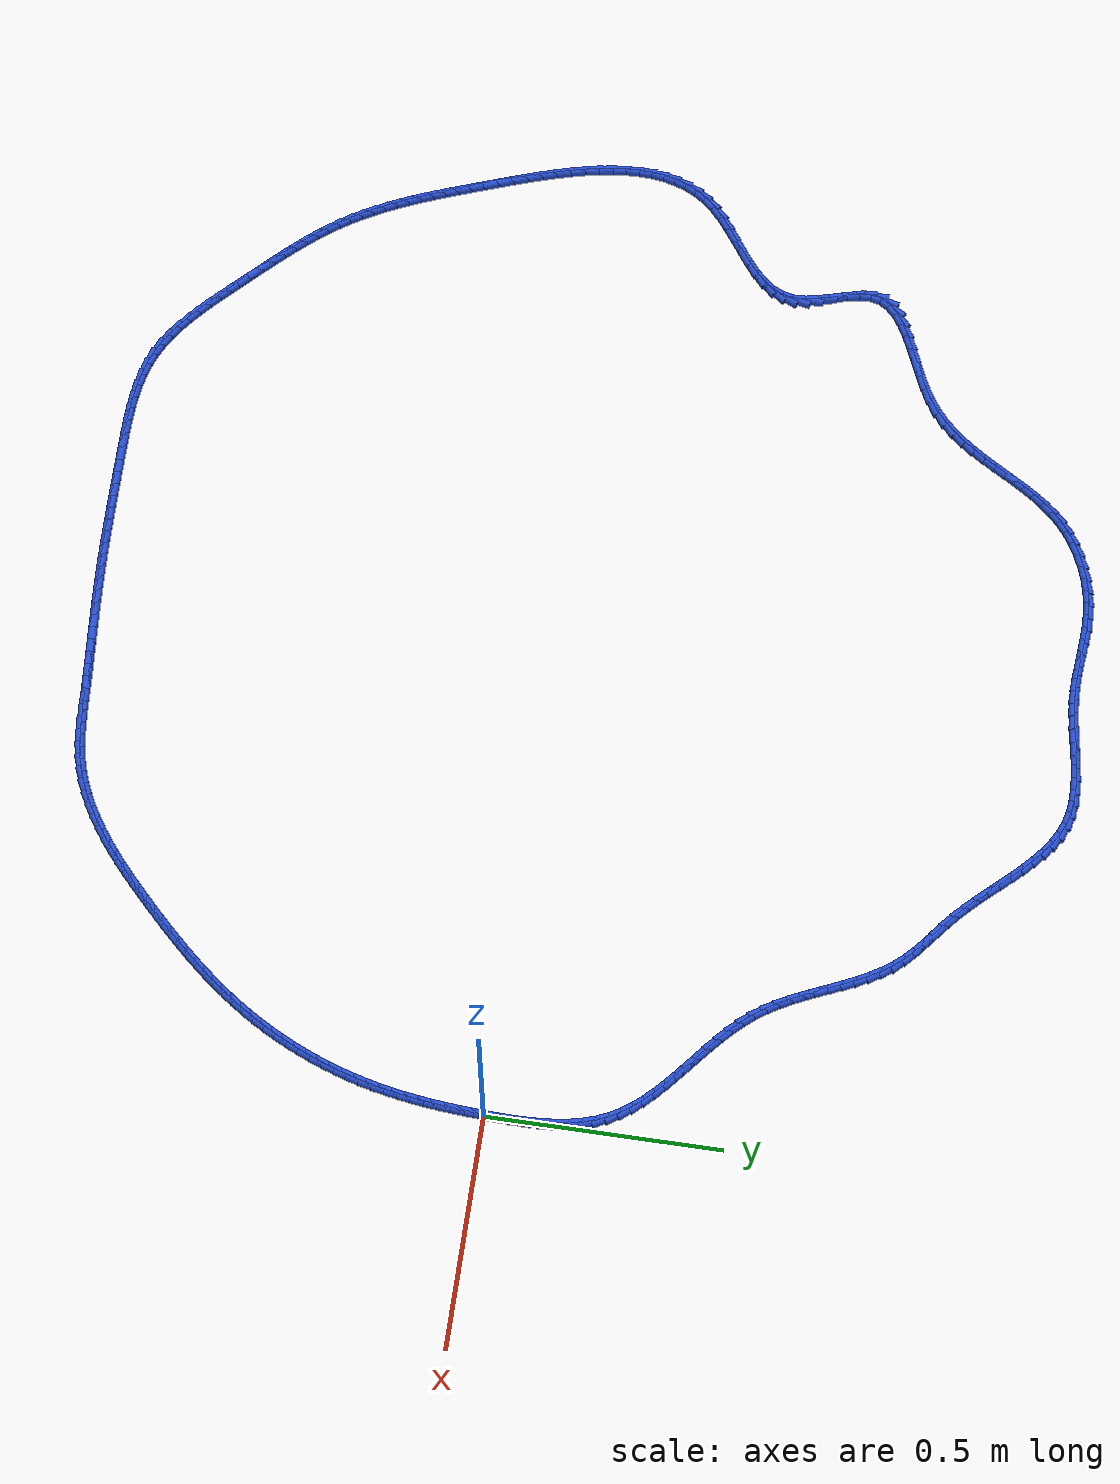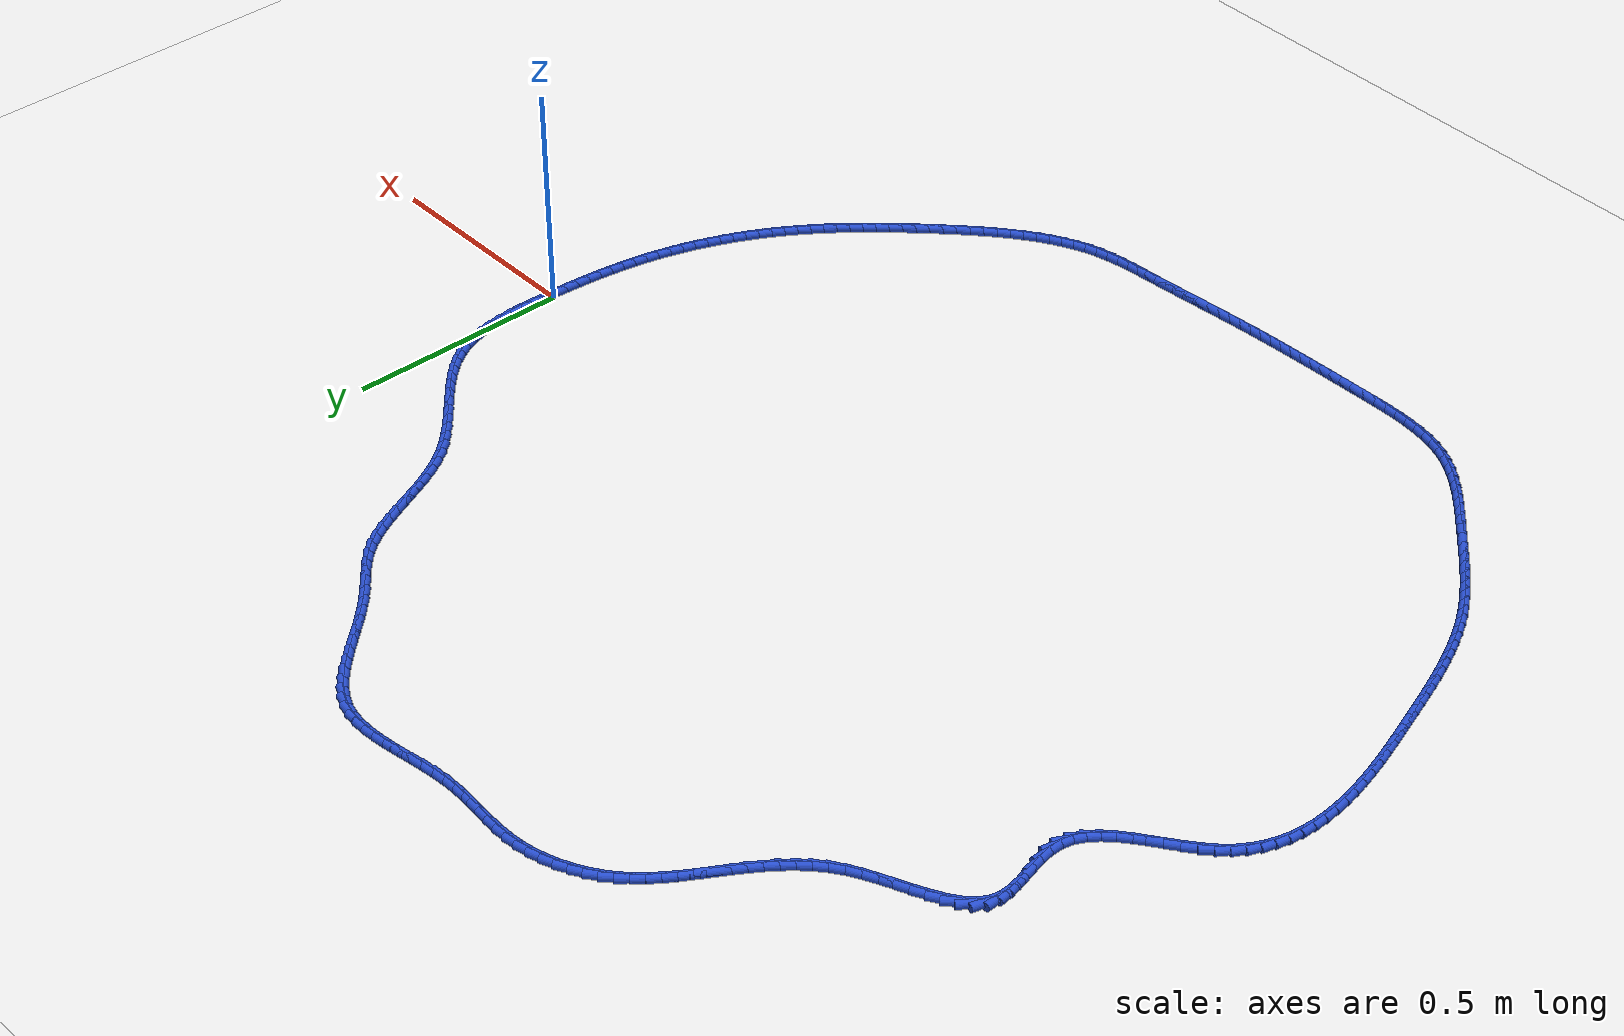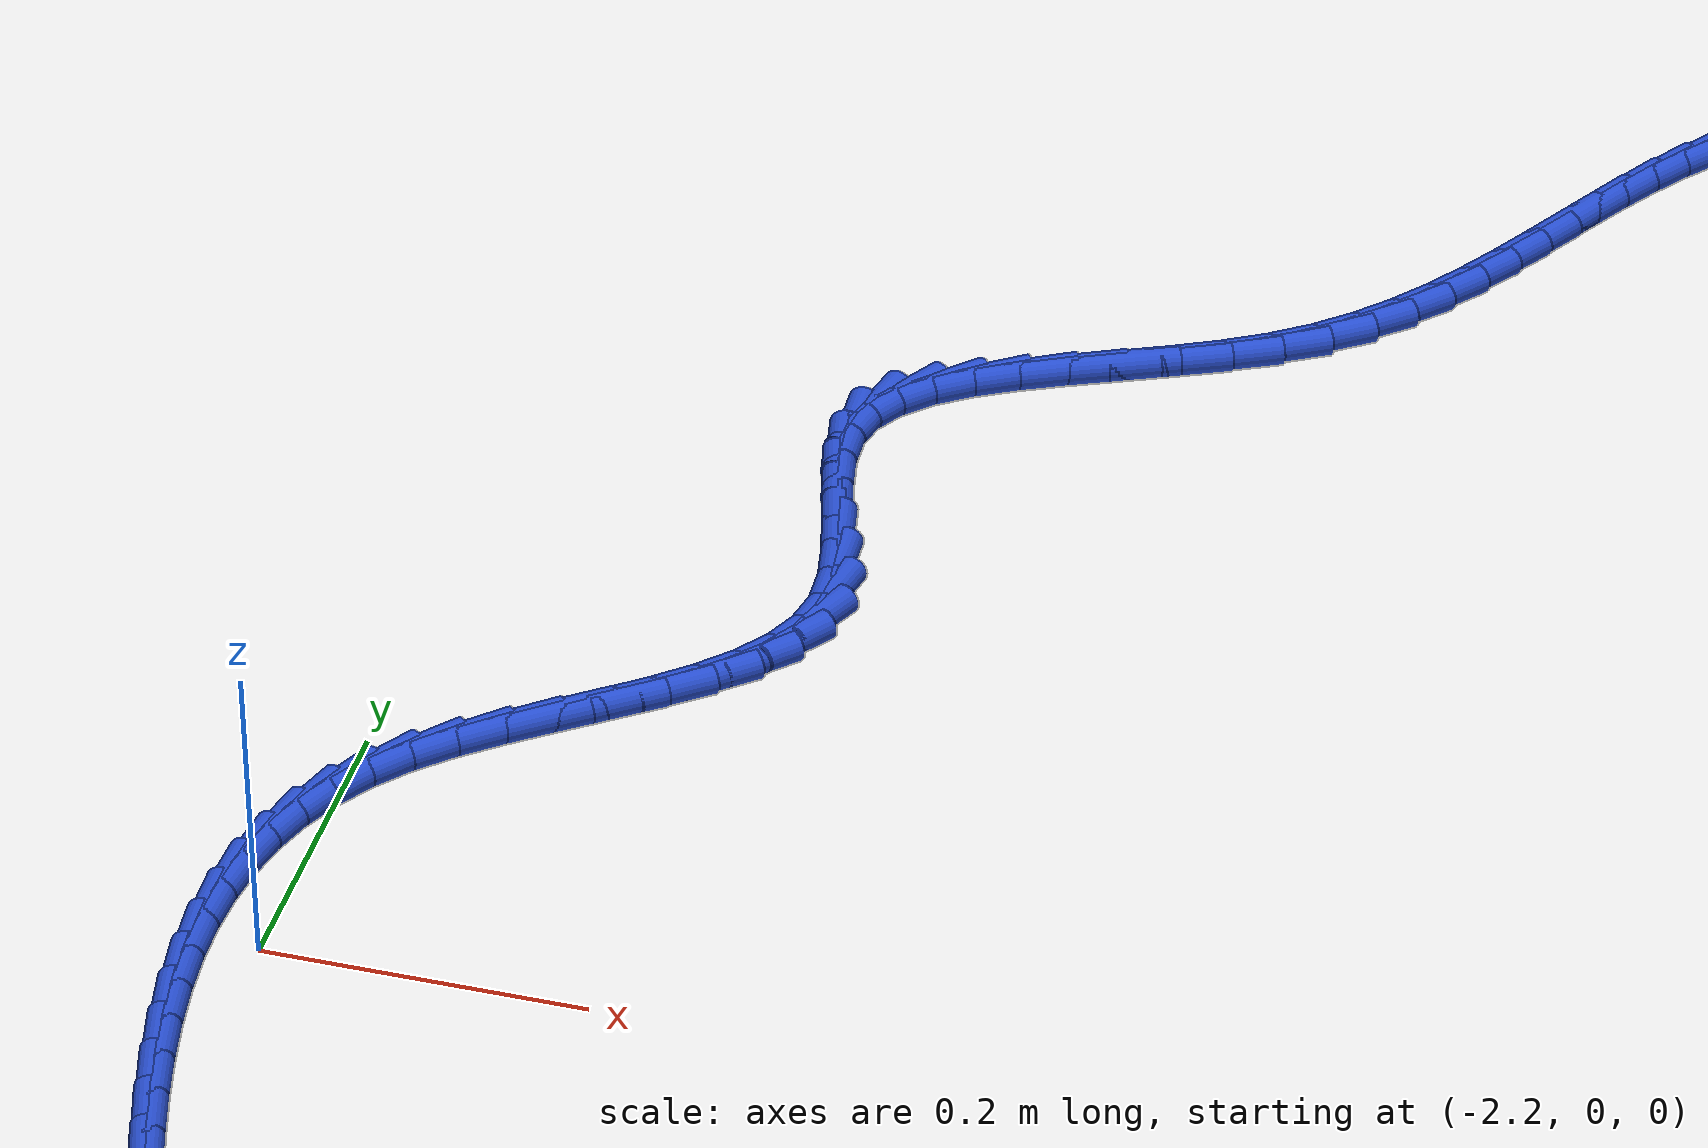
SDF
<sdf version="1.6">
 <world name="default">
  <light name="sun" type="directional">
   <pose>0 0 10 0 -0 0</pose>
   <diffuse>0.8 0.8 0.8 1</diffuse>
   <specular>0.2 0.2 0.2 1</specular>
   <attenuation>
    <range>1000</range>
    <constant>0.9</constant>
    <linear>0.01</linear>
    <quadratic>0.001</quadratic>
   </attenuation>
   <direction>-0.5 0.1 -0.9</direction>
  </light>
  <model name="ground_plane">
   <static>1</static>
   <link name="link">
    <collision name="collision">
     <geometry><plane><normal>0 0 1</normal><size>100 100</size></plane></geometry>
     <surface><friction><ode><mu>100</mu><mu2>50</mu2></ode></friction></surface>
    </collision>
    <visual name="visual">
     <cast_shadows>0</cast_shadows>
     <geometry><plane><normal>0 0 1</normal><size>100 100</size></plane></geometry>
     <material>
      <script><uri>file://media/materials/scripts/gazebo.material</uri><name>Gazebo/WhiteGlow</name></script>
     </material>
    </visual>
   </link>
  </model>
  <gravity>0 0 -9.8</gravity>
  <magnetic_field>6e-06 2.3e-05 -4.2e-05</magnetic_field>
  <atmosphere type="adiabatic"/>
  <physics name="default_physics" default="0" type="ode">
   <max_step_size>0.001</max_step_size>
   <real_time_factor>1</real_time_factor>
   <real_time_update_rate>1000</real_time_update_rate>
  </physics>
  <scene><ambient>0.4 0.4 0.4 1</ambient><background>0.7 0.7 0.7 1</background><shadows>1</shadows></scene>
  <spherical_coordinates>
   <surface_model>EARTH_WGS84</surface_model>
   <latitude_deg>0</latitude_deg>
   <longitude_deg>0</longitude_deg>
   <elevation>0</elevation>
   <heading_deg>0</heading_deg>
  </spherical_coordinates>
  <model name="line">
   <link name="link_0">
    <pose>-1.0625181290357943e-17 3.469446951953614e-17 0.01 0 1.57 1.5319547142780796</pose>
    <collision name="collision">
     <geometry><cylinder><radius>0.01</radius><length>0.08</length></cylinder></geometry>
    </collision>
    <visual name="visual">
     <material>
      <script><name>Gazebo/Blue</name><uri>file://media/materials/scripts/gazebo.material</uri></script>
     </material>
     <geometry><cylinder><radius>0.01</radius><length>0.08</length></cylinder></geometry>
    </visual>
   </link>
   <link name="link_1">
    <pose>0.0011593005383207513 0.029831858247192315 0.01 0 1.57 1.551653794150923</pose>
    <collision name="collision">
     <geometry><cylinder><radius>0.01</radius><length>0.08</length></cylinder></geometry>
    </collision>
    <visual name="visual">
     <material>
      <script><name>Gazebo/Blue</name><uri>file://media/materials/scripts/gazebo.material</uri></script>
     </material>
     <geometry><cylinder><radius>0.01</radius><length>0.08</length></cylinder></geometry>
    </visual>
   </link>
   <link name="link_2">
    <pose>0.0017334703667894098 0.05982264918177421 0.01 0 1.57 -1.5616173898954255</pose>
    <collision name="collision">
     <geometry><cylinder><radius>0.01</radius><length>0.08</length></cylinder></geometry>
    </collision>
    <visual name="visual">
     <material>
      <script><name>Gazebo/Blue</name><uri>file://media/materials/scripts/gazebo.material</uri></script>
     </material>
     <geometry><cylinder><radius>0.01</radius><length>0.08</length></cylinder></geometry>
    </visual>
   </link>
   <link name="link_3">
    <pose>0.0014586774453710638 0.0897591447715395 0.01 0 1.57 -1.5240613971402666</pose>
    <collision name="collision">
     <geometry><cylinder><radius>0.01</radius><length>0.08</length></cylinder></geometry>
    </collision>
    <visual name="visual">
     <material>
      <script><name>Gazebo/Blue</name><uri>file://media/materials/scripts/gazebo.material</uri></script>
     </material>
     <geometry><cylinder><radius>0.01</radius><length>0.08</length></cylinder></geometry>
    </visual>
   </link>
   <link name="link_4">
    <pose>7.108973403081777e-05 0.119428116984282 0.01 0 1.57 -1.4763748488246935</pose>
    <collision name="collision">
     <geometry><cylinder><radius>0.01</radius><length>0.08</length></cylinder></geometry>
    </collision>
    <visual name="visual">
     <material>
      <script><name>Gazebo/Blue</name><uri>file://media/materials/scripts/gazebo.material</uri></script>
     </material>
     <geometry><cylinder><radius>0.01</radius><length>0.08</length></cylinder></geometry>
    </visual>
   </link>
   <link name="link_5">
    <pose>-0.002693124807266227 0.14861633778779562 0.01 0 1.57 -1.4174290479311944</pose>
    <collision name="collision">
     <geometry><cylinder><radius>0.01</radius><length>0.08</length></cylinder></geometry>
    </collision>
    <visual name="visual">
     <material>
      <script><name>Gazebo/Blue</name><uri>file://media/materials/scripts/gazebo.material</uri></script>
     </material>
     <geometry><cylinder><radius>0.01</radius><length>0.08</length></cylinder></geometry>
    </visual>
   </link>
   <link name="link_6">
    <pose>-0.007097798218554971 0.17711057914987416 0.01 0 1.57 -1.3459695303603756</pose>
    <collision name="collision">
     <geometry><cylinder><radius>0.01</radius><length>0.08</length></cylinder></geometry>
    </collision>
    <visual name="visual">
     <material>
      <script><name>Gazebo/Blue</name><uri>file://media/materials/scripts/gazebo.material</uri></script>
     </material>
     <geometry><cylinder><radius>0.01</radius><length>0.08</length></cylinder></geometry>
    </visual>
   </link>
   <link name="link_7">
    <pose>-0.013406762539870309 0.20469761303831147 0.01 0 1.57 -1.260826898898076</pose>
    <collision name="collision">
     <geometry><cylinder><radius>0.01</radius><length>0.08</length></cylinder></geometry>
    </collision>
    <visual name="visual">
     <material>
      <script><name>Gazebo/Blue</name><uri>file://media/materials/scripts/gazebo.material</uri></script>
     </material>
     <geometry><cylinder><radius>0.01</radius><length>0.08</length></cylinder></geometry>
    </visual>
   </link>
   <link name="link_8">
    <pose>-0.021883849811247136 0.23116421142090127 0.01 0 1.57 -1.1612822113886632</pose>
    <collision name="collision">
     <geometry><cylinder><radius>0.01</radius><length>0.08</length></cylinder></geometry>
    </collision>
    <visual name="visual">
     <material>
      <script><name>Gazebo/Blue</name><uri>file://media/materials/scripts/gazebo.material</uri></script>
     </material>
     <geometry><cylinder><radius>0.01</radius><length>0.08</length></cylinder></geometry>
    </visual>
   </link>
   <link name="link_9">
    <pose>-0.03279289207272036 0.25629714626543765 0.01 0 1.57 -1.050928193806608</pose>
    <collision name="collision">
     <geometry><cylinder><radius>0.01</radius><length>0.08</length></cylinder></geometry>
    </collision>
    <visual name="visual">
     <material>
      <script><name>Gazebo/Blue</name><uri>file://media/materials/scripts/gazebo.material</uri></script>
     </material>
     <geometry><cylinder><radius>0.01</radius><length>0.08</length></cylinder></geometry>
    </visual>
   </link>
   <link name="link_10">
    <pose>-0.04632335181983484 0.27993581333932704 0.01 0 1.57 -0.9497696811602896</pose>
    <collision name="collision">
     <geometry><cylinder><radius>0.01</radius><length>0.08</length></cylinder></geometry>
    </collision>
    <visual name="visual">
     <material>
      <script><name>Gazebo/Blue</name><uri>file://media/materials/scripts/gazebo.material</uri></script>
     </material>
     <geometry><cylinder><radius>0.01</radius><length>0.08</length></cylinder></geometry>
    </visual>
   </link>
   <link name="link_11">
    <pose>-0.06225784713813789 0.30220749102176536 0.01 0 1.57 -0.865689769817296</pose>
    <collision name="collision">
     <geometry><cylinder><radius>0.01</radius><length>0.08</length></cylinder></geometry>
    </collision>
    <visual name="visual">
     <material>
      <script><name>Gazebo/Blue</name><uri>file://media/materials/scripts/gazebo.material</uri></script>
     </material>
     <geometry><cylinder><radius>0.01</radius><length>0.08</length></cylinder></geometry>
    </visual>
   </link>
   <link name="link_12">
    <pose>-0.08024057655857325 0.32333740320114723 0.01 0 1.57 -0.7988951021014247</pose>
    <collision name="collision">
     <geometry><cylinder><radius>0.01</radius><length>0.08</length></cylinder></geometry>
    </collision>
    <visual name="visual">
     <material>
      <script><name>Gazebo/Blue</name><uri>file://media/materials/scripts/gazebo.material</uri></script>
     </material>
     <geometry><cylinder><radius>0.01</radius><length>0.08</length></cylinder></geometry>
    </visual>
   </link>
   <link name="link_13">
    <pose>-0.09991562335821562 0.34355085531936547 0.01 0 1.57 -0.7486761550408071</pose>
    <collision name="collision">
     <geometry><cylinder><radius>0.01</radius><length>0.08</length></cylinder></geometry>
    </collision>
    <visual name="visual">
     <material>
      <script><name>Gazebo/Blue</name><uri>file://media/materials/scripts/gazebo.material</uri></script>
     </material>
     <geometry><cylinder><radius>0.01</radius><length>0.08</length></cylinder></geometry>
    </visual>
   </link>
   <link name="link_14">
    <pose>-0.12092707081413981 0.3630731528183128 0.01 0 1.57 -0.7140069344762455</pose>
    <collision name="collision">
     <geometry><cylinder><radius>0.01</radius><length>0.08</length></cylinder></geometry>
    </collision>
    <visual name="visual">
     <material>
      <script><name>Gazebo/Blue</name><uri>file://media/materials/scripts/gazebo.material</uri></script>
     </material>
     <geometry><cylinder><radius>0.01</radius><length>0.08</length></cylinder></geometry>
    </visual>
   </link>
   <link name="link_15">
    <pose>-0.14291900220342058 0.3821296011398818 0.01 0 1.57 -0.6939241642197241</pose>
    <collision name="collision">
     <geometry><cylinder><radius>0.01</radius><length>0.08</length></cylinder></geometry>
    </collision>
    <visual name="visual">
     <material>
      <script><name>Gazebo/Blue</name><uri>file://media/materials/scripts/gazebo.material</uri></script>
     </material>
     <geometry><cylinder><radius>0.01</radius><length>0.08</length></cylinder></geometry>
    </visual>
   </link>
   <link name="link_16">
    <pose>-0.1655355008031327 0.4009455057259656 0.01 0 1.57 -0.687727375319172</pose>
    <collision name="collision">
     <geometry><cylinder><radius>0.01</radius><length>0.08</length></cylinder></geometry>
    </collision>
    <visual name="visual">
     <material>
      <script><name>Gazebo/Blue</name><uri>file://media/materials/scripts/gazebo.material</uri></script>
     </material>
     <geometry><cylinder><radius>0.01</radius><length>0.08</length></cylinder></geometry>
    </visual>
   </link>
   <link name="link_17">
    <pose>-0.1884206498903509 0.41974617201845654 0.01 0 1.57 -0.6950617150823086</pose>
    <collision name="collision">
     <geometry><cylinder><radius>0.01</radius><length>0.08</length></cylinder></geometry>
    </collision>
    <visual name="visual">
     <material>
      <script><name>Gazebo/Blue</name><uri>file://media/materials/scripts/gazebo.material</uri></script>
     </material>
     <geometry><cylinder><radius>0.01</radius><length>0.08</length></cylinder></geometry>
    </visual>
   </link>
   <link name="link_18">
    <pose>-0.21121853274215002 0.43875690545924756 0.01 0 1.57 -0.7159278931651797</pose>
    <collision name="collision">
     <geometry><cylinder><radius>0.01</radius><length>0.08</length></cylinder></geometry>
    </collision>
    <visual name="visual">
     <material>
      <script><name>Gazebo/Blue</name><uri>file://media/materials/scripts/gazebo.material</uri></script>
     </material>
     <geometry><cylinder><radius>0.01</radius><length>0.08</length></cylinder></geometry>
    </visual>
   </link>
   <link name="link_19">
    <pose>-0.23357323263560484 0.4582030114902314 0.01 0 1.57 -0.7506370095609386</pose>
    <collision name="collision">
     <geometry><cylinder><radius>0.01</radius><length>0.08</length></cylinder></geometry>
    </collision>
    <visual name="visual">
     <material>
      <script><name>Gazebo/Blue</name><uri>file://media/materials/scripts/gazebo.material</uri></script>
     </material>
     <geometry><cylinder><radius>0.01</radius><length>0.08</length></cylinder></geometry>
    </visual>
   </link>
   <link name="link_20">
    <pose>-0.25512883284779003 0.47830979555330083 0.01 0 1.57 -0.7997034398308498</pose>
    <collision name="collision">
     <geometry><cylinder><radius>0.01</radius><length>0.08</length></cylinder></geometry>
    </collision>
    <visual name="visual">
     <material>
      <script><name>Gazebo/Blue</name><uri>file://media/materials/scripts/gazebo.material</uri></script>
     </material>
     <geometry><cylinder><radius>0.01</radius><length>0.08</length></cylinder></geometry>
    </visual>
   </link>
   <link name="link_21">
    <pose>-0.2755294166557804 0.49930256309034843 0.01 0 1.57 -0.8636502245459102</pose>
    <collision name="collision">
     <geometry><cylinder><radius>0.01</radius><length>0.08</length></cylinder></geometry>
    </collision>
    <visual name="visual">
     <material>
      <script><name>Gazebo/Blue</name><uri>file://media/materials/scripts/gazebo.material</uri></script>
     </material>
     <geometry><cylinder><radius>0.01</radius><length>0.08</length></cylinder></geometry>
    </visual>
   </link>
   <link name="link_22">
    <pose>-0.2944190673366509 0.5214066195432674 0.01 0 1.57 -0.9412953103915688</pose>
    <collision name="collision">
     <geometry><cylinder><radius>0.01</radius><length>0.08</length></cylinder></geometry>
    </collision>
    <visual name="visual">
     <material>
      <script><name>Gazebo/Blue</name><uri>file://media/materials/scripts/gazebo.material</uri></script>
     </material>
     <geometry><cylinder><radius>0.01</radius><length>0.08</length></cylinder></geometry>
    </visual>
   </link>
   <link name="link_23">
    <pose>-0.3114749705582306 0.5448237753493216 0.01 0 1.57 -1.01484189505734</pose>
    <collision name="collision">
     <geometry><cylinder><radius>0.01</radius><length>0.08</length></cylinder></geometry>
    </collision>
    <visual name="visual">
     <material>
      <script><name>Gazebo/Blue</name><uri>file://media/materials/scripts/gazebo.material</uri></script>
     </material>
     <geometry><cylinder><radius>0.01</radius><length>0.08</length></cylinder></geometry>
    </visual>
   </link>
   <link name="link_24">
    <pose>-0.32678489501437175 0.5694644224144635 0.01 0 1.57 -1.0721115181008116</pose>
    <collision name="collision">
     <geometry><cylinder><radius>0.01</radius><length>0.08</length></cylinder></geometry>
    </collision>
    <visual name="visual">
     <material>
      <script><name>Gazebo/Blue</name><uri>file://media/materials/scripts/gazebo.material</uri></script>
     </material>
     <geometry><cylinder><radius>0.01</radius><length>0.08</length></cylinder></geometry>
    </visual>
   </link>
   <link name="link_25">
    <pose>-0.3407142738504298 0.595041875411718 0.01 0 1.57 -1.1130361572881824</pose>
    <collision name="collision">
     <geometry><cylinder><radius>0.01</radius><length>0.08</length></cylinder></geometry>
    </collision>
    <visual name="visual">
     <material>
      <script><name>Gazebo/Blue</name><uri>file://media/materials/scripts/gazebo.material</uri></script>
     </material>
     <geometry><cylinder><radius>0.01</radius><length>0.08</length></cylinder></geometry>
    </visual>
   </link>
   <link name="link_26">
    <pose>-0.353633777155769 0.6212657320009012 0.01 0 1.57 -1.1379956186312776</pose>
    <collision name="collision">
     <geometry><cylinder><radius>0.01</radius><length>0.08</length></cylinder></geometry>
    </collision>
    <visual name="visual">
     <material>
      <script><name>Gazebo/Blue</name><uri>file://media/materials/scripts/gazebo.material</uri></script>
     </material>
     <geometry><cylinder><radius>0.01</radius><length>0.08</length></cylinder></geometry>
    </visual>
   </link>
   <link name="link_27">
    <pose>-0.36591407501975276 0.6478455898418284 0.01 0 1.57 -1.147277612152728</pose>
    <collision name="collision">
     <geometry><cylinder><radius>0.01</radius><length>0.08</length></cylinder></geometry>
    </collision>
    <visual name="visual">
     <material>
      <script><name>Gazebo/Blue</name><uri>file://media/materials/scripts/gazebo.material</uri></script>
     </material>
     <geometry><cylinder><radius>0.01</radius><length>0.08</length></cylinder></geometry>
    </visual>
   </link>
   <link name="link_28">
    <pose>-0.37792583753174536 0.6744910465943161 0.01 0 1.57 -1.1408954569344043</pose>
    <collision name="collision">
     <geometry><cylinder><radius>0.01</radius><length>0.08</length></cylinder></geometry>
    </collision>
    <visual name="visual">
     <material>
      <script><name>Gazebo/Blue</name><uri>file://media/materials/scripts/gazebo.material</uri></script>
     </material>
     <geometry><cylinder><radius>0.01</radius><length>0.08</length></cylinder></geometry>
    </visual>
   </link>
   <link name="link_29">
    <pose>-0.3900397347811102 0.7009116999181793 0.01 0 1.57 -1.118515785905297</pose>
    <collision name="collision">
     <geometry><cylinder><radius>0.01</radius><length>0.08</length></cylinder></geometry>
    </collision>
    <visual name="visual">
     <material>
      <script><name>Gazebo/Blue</name><uri>file://media/materials/scripts/gazebo.material</uri></script>
     </material>
     <geometry><cylinder><radius>0.01</radius><length>0.08</length></cylinder></geometry>
    </visual>
   </link>
   <link name="link_30">
    <pose>-0.40262643685721144 0.7268171474732343 0.01 0 1.57 -1.0794877167922095</pose>
    <collision name="collision">
     <geometry><cylinder><radius>0.01</radius><length>0.08</length></cylinder></geometry>
    </collision>
    <visual name="visual">
     <material>
      <script><name>Gazebo/Blue</name><uri>file://media/materials/scripts/gazebo.material</uri></script>
     </material>
     <geometry><cylinder><radius>0.01</radius><length>0.08</length></cylinder></geometry>
    </visual>
   </link>
   <link name="link_31">
    <pose>-0.4160566138494127 0.7519169869192968 0.01 0 1.57 -1.022996006503441</pose>
    <collision name="collision">
     <geometry><cylinder><radius>0.01</radius><length>0.08</length></cylinder></geometry>
    </collision>
    <visual name="visual">
     <material>
      <script><name>Gazebo/Blue</name><uri>file://media/materials/scripts/gazebo.material</uri></script>
     </material>
     <geometry><cylinder><radius>0.01</radius><length>0.08</length></cylinder></geometry>
    </visual>
   </link>
   <link name="link_32">
    <pose>-0.43070093584707814 0.7759208159161826 0.01 0 1.57 -0.948388395120563</pose>
    <collision name="collision">
     <geometry><cylinder><radius>0.01</radius><length>0.08</length></cylinder></geometry>
    </collision>
    <visual name="visual">
     <material>
      <script><name>Gazebo/Blue</name><uri>file://media/materials/scripts/gazebo.material</uri></script>
     </material>
     <geometry><cylinder><radius>0.01</radius><length>0.08</length></cylinder></geometry>
    </visual>
   </link>
   <link name="link_33">
    <pose>-0.4469300729395711 0.798538232123707 0.01 0 1.57 -0.8561327929687194</pose>
    <collision name="collision">
     <geometry><cylinder><radius>0.01</radius><length>0.08</length></cylinder></geometry>
    </collision>
    <visual name="visual">
     <material>
      <script><name>Gazebo/Blue</name><uri>file://media/materials/scripts/gazebo.material</uri></script>
     </material>
     <geometry><cylinder><radius>0.01</radius><length>0.08</length></cylinder></geometry>
    </visual>
   </link>
   <link name="link_34">
    <pose>-0.4651066293399603 0.8194869233176152 0.01 0 1.57 -0.7661928640508829</pose>
    <collision name="collision">
     <geometry><cylinder><radius>0.01</radius><length>0.08</length></cylinder></geometry>
    </collision>
    <visual name="visual">
     <material>
      <script><name>Gazebo/Blue</name><uri>file://media/materials/scripts/gazebo.material</uri></script>
     </material>
     <geometry><cylinder><radius>0.01</radius><length>0.08</length></cylinder></geometry>
    </visual>
   </link>
   <link name="link_35">
    <pose>-0.48522850469955414 0.8388503778483706 0.01 0 1.57 -0.7056615643781543</pose>
    <collision name="collision">
     <geometry><cylinder><radius>0.01</radius><length>0.08</length></cylinder></geometry>
    </collision>
    <visual name="visual">
     <material>
      <script><name>Gazebo/Blue</name><uri>file://media/materials/scripts/gazebo.material</uri></script>
     </material>
     <geometry><cylinder><radius>0.01</radius><length>0.08</length></cylinder></geometry>
    </visual>
   </link>
   <link name="link_36">
    <pose>-0.5067879211159138 0.8572192812862633 0.01 0 1.57 -0.6758474805664169</pose>
    <collision name="collision">
     <geometry><cylinder><radius>0.01</radius><length>0.08</length></cylinder></geometry>
    </collision>
    <visual name="visual">
     <material>
      <script><name>Gazebo/Blue</name><uri>file://media/materials/scripts/gazebo.material</uri></script>
     </material>
     <geometry><cylinder><radius>0.01</radius><length>0.08</length></cylinder></geometry>
    </visual>
   </link>
   <link name="link_37">
    <pose>-0.5292398928270186 0.8752216388785128 0.01 0 1.57 -0.6753873899877938</pose>
    <collision name="collision">
     <geometry><cylinder><radius>0.01</radius><length>0.08</length></cylinder></geometry>
    </collision>
    <visual name="visual">
     <material>
      <script><name>Gazebo/Blue</name><uri>file://media/materials/scripts/gazebo.material</uri></script>
     </material>
     <geometry><cylinder><radius>0.01</radius><length>0.08</length></cylinder></geometry>
    </visual>
   </link>
   <link name="link_38">
    <pose>-0.5520394340708475 0.8934854558723373 0.01 0 1.57 -0.702988895995224</pose>
    <collision name="collision">
     <geometry><cylinder><radius>0.01</radius><length>0.08</length></cylinder></geometry>
    </collision>
    <visual name="visual">
     <material>
      <script><name>Gazebo/Blue</name><uri>file://media/materials/scripts/gazebo.material</uri></script>
     </material>
     <geometry><cylinder><radius>0.01</radius><length>0.08</length></cylinder></geometry>
    </visual>
   </link>
   <link name="link_39">
    <pose>-0.5746415590853801 0.9126387375149559 0.01 0 1.57 -0.7503348897162581</pose>
    <collision name="collision">
     <geometry><cylinder><radius>0.01</radius><length>0.08</length></cylinder></geometry>
    </collision>
    <visual name="visual">
     <material>
      <script><name>Gazebo/Blue</name><uri>file://media/materials/scripts/gazebo.material</uri></script>
     </material>
     <geometry><cylinder><radius>0.01</radius><length>0.08</length></cylinder></geometry>
    </visual>
   </link>
   <link name="link_40">
    <pose>-0.5966208691486082 0.9331283379953533 0.01 0 1.57 -0.788460525124303</pose>
    <collision name="collision">
     <geometry><cylinder><radius>0.01</radius><length>0.08</length></cylinder></geometry>
    </collision>
    <visual name="visual">
     <material>
      <script><name>Gazebo/Blue</name><uri>file://media/materials/scripts/gazebo.material</uri></script>
     </material>
     <geometry><cylinder><radius>0.01</radius><length>0.08</length></cylinder></geometry>
    </visual>
   </link>
   <link name="link_41">
    <pose>-0.618033167621468 0.9546721841326212 0.01 0 1.57 -0.8111275321198776</pose>
    <collision name="collision">
     <geometry><cylinder><radius>0.01</radius><length>0.08</length></cylinder></geometry>
    </collision>
    <visual name="visual">
     <material>
      <script><name>Gazebo/Blue</name><uri>file://media/materials/scripts/gazebo.material</uri></script>
     </material>
     <geometry><cylinder><radius>0.01</radius><length>0.08</length></cylinder></geometry>
    </visual>
   </link>
   <link name="link_42">
    <pose>-0.6390552761179606 0.976804883678784 0.01 0 1.57 -0.8189957309504938</pose>
    <collision name="collision">
     <geometry><cylinder><radius>0.01</radius><length>0.08</length></cylinder></geometry>
    </collision>
    <visual name="visual">
     <material>
      <script><name>Gazebo/Blue</name><uri>file://media/materials/scripts/gazebo.material</uri></script>
     </material>
     <geometry><cylinder><radius>0.01</radius><length>0.08</length></cylinder></geometry>
    </visual>
   </link>
   <link name="link_43">
    <pose>-0.6598640162530264 0.9990610443844463 0.01 0 1.57 -0.8121458686661917</pose>
    <collision name="collision">
     <geometry><cylinder><radius>0.01</radius><length>0.08</length></cylinder></geometry>
    </collision>
    <visual name="visual">
     <material>
      <script><name>Gazebo/Blue</name><uri>file://media/materials/scripts/gazebo.material</uri></script>
     </material>
     <geometry><cylinder><radius>0.01</radius><length>0.08</length></cylinder></geometry>
    </visual>
   </link>
   <link name="link_44">
    <pose>-0.6806362096416035 1.020975274000211 0.01 0 1.57 -0.7900254724383622</pose>
    <collision name="collision">
     <geometry><cylinder><radius>0.01</radius><length>0.08</length></cylinder></geometry>
    </collision>
    <visual name="visual">
     <material>
      <script><name>Gazebo/Blue</name><uri>file://media/materials/scripts/gazebo.material</uri></script>
     </material>
     <geometry><cylinder><radius>0.01</radius><length>0.08</length></cylinder></geometry>
    </visual>
   </link>
   <link name="link_45">
    <pose>-0.7015486778986324 1.0420821802766824 0.01 0 1.57 -0.7514305601705806</pose>
    <collision name="collision">
     <geometry><cylinder><radius>0.01</radius><length>0.08</length></cylinder></geometry>
    </collision>
    <visual name="visual">
     <material>
      <script><name>Gazebo/Blue</name><uri>file://media/materials/scripts/gazebo.material</uri></script>
     </material>
     <geometry><cylinder><radius>0.01</radius><length>0.08</length></cylinder></geometry>
    </visual>
   </link>
   <link name="link_46">
    <pose>-0.7227782426390519 1.0619163709644648 0.01 0 1.57 -0.6945529811503913</pose>
    <collision name="collision">
     <geometry><cylinder><radius>0.01</radius><length>0.08</length></cylinder></geometry>
    </collision>
    <visual name="visual">
     <material>
      <script><name>Gazebo/Blue</name><uri>file://media/materials/scripts/gazebo.material</uri></script>
     </material>
     <geometry><cylinder><radius>0.01</radius><length>0.08</length></cylinder></geometry>
    </visual>
   </link>
   <link name="link_47">
    <pose>-0.744501725477802 1.0800124538141618 0.01 0 1.57 -0.6171886799488164</pose>
    <collision name="collision">
     <geometry><cylinder><radius>0.01</radius><length>0.08</length></cylinder></geometry>
    </collision>
    <visual name="visual">
     <material>
      <script><name>Gazebo/Blue</name><uri>file://media/materials/scripts/gazebo.material</uri></script>
     </material>
     <geometry><cylinder><radius>0.01</radius><length>0.08</length></cylinder></geometry>
    </visual>
   </link>
   <link name="link_48">
    <pose>-0.7668959480298216 1.0959050365763767 0.01 0 1.57 -0.5172846772544478</pose>
    <collision name="collision">
     <geometry><cylinder><radius>0.01</radius><length>0.08</length></cylinder></geometry>
    </collision>
    <visual name="visual">
     <material>
      <script><name>Gazebo/Blue</name><uri>file://media/materials/scripts/gazebo.material</uri></script>
     </material>
     <geometry><cylinder><radius>0.01</radius><length>0.08</length></cylinder></geometry>
    </visual>
   </link>
   <link name="link_49">
    <pose>-0.7901377319100504 1.1091287270017145 0.01 0 1.57 -0.39403604646313295</pose>
    <collision name="collision">
     <geometry><cylinder><radius>0.01</radius><length>0.08</length></cylinder></geometry>
    </collision>
    <visual name="visual">
     <material>
      <script><name>Gazebo/Blue</name><uri>file://media/materials/scripts/gazebo.material</uri></script>
     </material>
     <geometry><cylinder><radius>0.01</radius><length>0.08</length></cylinder></geometry>
    </visual>
   </link>
   <link name="link_50">
    <pose>-0.8144038987334277 1.119218132840778 0.01 0 1.57 -0.25263680146952816</pose>
    <collision name="collision">
     <geometry><cylinder><radius>0.01</radius><length>0.08</length></cylinder></geometry>
    </collision>
    <visual name="visual">
     <material>
      <script><name>Gazebo/Blue</name><uri>file://media/materials/scripts/gazebo.material</uri></script>
     </material>
     <geometry><cylinder><radius>0.01</radius><length>0.08</length></cylinder></geometry>
    </visual>
   </link>
   <link name="link_51">
    <pose>-0.8398457127534601 1.1257860017441947 0.01 0 1.57 -0.12362220827639893</pose>
    <collision name="collision">
     <geometry><cylinder><radius>0.01</radius><length>0.08</length></cylinder></geometry>
    </collision>
    <visual name="visual">
     <material>
      <script><name>Gazebo/Blue</name><uri>file://media/materials/scripts/gazebo.material</uri></script>
     </material>
     <geometry><cylinder><radius>0.01</radius><length>0.08</length></cylinder></geometry>
    </visual>
   </link>
   <link name="link_52">
    <pose>-0.8664047725910601 1.1290861198208022 0.01 0 1.57 -0.021815859087895323</pose>
    <collision name="collision">
     <geometry><cylinder><radius>0.01</radius><length>0.08</length></cylinder></geometry>
    </collision>
    <visual name="visual">
     <material>
      <script><name>Gazebo/Blue</name><uri>file://media/materials/scripts/gazebo.material</uri></script>
     </material>
     <geometry><cylinder><radius>0.01</radius><length>0.08</length></cylinder></geometry>
    </visual>
   </link>
   <link name="link_53">
    <pose>-0.8939199082076889 1.1296864813889231 0.01 0 1.57 0.05396653819626558</pose>
    <collision name="collision">
     <geometry><cylinder><radius>0.01</radius><length>0.08</length></cylinder></geometry>
    </collision>
    <visual name="visual">
     <material>
      <script><name>Gazebo/Blue</name><uri>file://media/materials/scripts/gazebo.material</uri></script>
     </material>
     <geometry><cylinder><radius>0.01</radius><length>0.08</length></cylinder></geometry>
    </visual>
   </link>
   <link name="link_54">
    <pose>-0.9222292434391571 1.1281572396981867 0.01 0 1.57 0.10631889022531293</pose>
    <collision name="collision">
     <geometry><cylinder><radius>0.01</radius><length>0.08</length></cylinder></geometry>
    </collision>
    <visual name="visual">
     <material>
      <script><name>Gazebo/Blue</name><uri>file://media/materials/scripts/gazebo.material</uri></script>
     </material>
     <geometry><cylinder><radius>0.01</radius><length>0.08</length></cylinder></geometry>
    </visual>
   </link>
   <link name="link_55">
    <pose>-0.9511709021212758 1.1250685479982225 0.01 0 1.57 0.1377716470293281</pose>
    <collision name="collision">
     <geometry><cylinder><radius>0.01</radius><length>0.08</length></cylinder></geometry>
    </collision>
    <visual name="visual">
     <material>
      <script><name>Gazebo/Blue</name><uri>file://media/materials/scripts/gazebo.material</uri></script>
     </material>
     <geometry><cylinder><radius>0.01</radius><length>0.08</length></cylinder></geometry>
    </visual>
   </link>
   <link name="link_56">
    <pose>-0.9805830080898551 1.1209905595386602 0.01 0 1.57 0.15017404260625164</pose>
    <collision name="collision">
     <geometry><cylinder><radius>0.01</radius><length>0.08</length></cylinder></geometry>
    </collision>
    <visual name="visual">
     <material>
      <script><name>Gazebo/Blue</name><uri>file://media/materials/scripts/gazebo.material</uri></script>
     </material>
     <geometry><cylinder><radius>0.01</radius><length>0.08</length></cylinder></geometry>
    </visual>
   </link>
   <link name="link_57">
    <pose>-1.0103036851807052 1.1164934275691285 0.01 0 1.57 0.14449984826473888</pose>
    <collision name="collision">
     <geometry><cylinder><radius>0.01</radius><length>0.08</length></cylinder></geometry>
    </collision>
    <visual name="visual">
     <material>
      <script><name>Gazebo/Blue</name><uri>file://media/materials/scripts/gazebo.material</uri></script>
     </material>
     <geometry><cylinder><radius>0.01</radius><length>0.08</length></cylinder></geometry>
    </visual>
   </link>
   <link name="link_58">
    <pose>-1.040171057229638 1.1121473053392583 0.01 0 1.57 0.12083864137538612</pose>
    <collision name="collision">
     <geometry><cylinder><radius>0.01</radius><length>0.08</length></cylinder></geometry>
    </collision>
    <visual name="visual">
     <material>
      <script><name>Gazebo/Blue</name><uri>file://media/materials/scripts/gazebo.material</uri></script>
     </material>
     <geometry><cylinder><radius>0.01</radius><length>0.08</length></cylinder></geometry>
    </visual>
   </link>
   <link name="link_59">
    <pose>-1.0700232480724636 1.108522346098678 0.01 0 1.57 0.07847817109037461</pose>
    <collision name="collision">
     <geometry><cylinder><radius>0.01</radius><length>0.08</length></cylinder></geometry>
    </collision>
    <visual name="visual">
     <material>
      <script><name>Gazebo/Blue</name><uri>file://media/materials/scripts/gazebo.material</uri></script>
     </material>
     <geometry><cylinder><radius>0.01</radius><length>0.08</length></cylinder></geometry>
    </visual>
   </link>
   <link name="link_60">
    <pose>-1.099698381544992 1.1061887030970174 0.01 0 1.57 0.018947330778175637</pose>
    <collision name="collision">
     <geometry><cylinder><radius>0.01</radius><length>0.08</length></cylinder></geometry>
    </collision>
    <visual name="visual">
     <material>
      <script><name>Gazebo/Blue</name><uri>file://media/materials/scripts/gazebo.material</uri></script>
     </material>
     <geometry><cylinder><radius>0.01</radius><length>0.08</length></cylinder></geometry>
    </visual>
   </link>
   <link name="link_61">
    <pose>-1.1290511345351344 1.1056324802136825 0.01 0 1.57 -0.034059775241199367</pose>
    <collision name="collision">
     <geometry><cylinder><radius>0.01</radius><length>0.08</length></cylinder></geometry>
    </collision>
    <visual name="visual">
     <material>
      <script><name>Gazebo/Blue</name><uri>file://media/materials/scripts/gazebo.material</uri></script>
     </material>
     <geometry><cylinder><radius>0.01</radius><length>0.08</length></cylinder></geometry>
    </visual>
   </link>
   <link name="link_62">
    <pose>-1.158077645581702 1.1066214991287058 0.01 0 1.57 -0.06725723691217136</pose>
    <collision name="collision">
     <geometry><cylinder><radius>0.01</radius><length>0.08</length></cylinder></geometry>
    </collision>
    <visual name="visual">
     <material>
      <script><name>Gazebo/Blue</name><uri>file://media/materials/scripts/gazebo.material</uri></script>
     </material>
     <geometry><cylinder><radius>0.01</radius><length>0.08</length></cylinder></geometry>
    </visual>
   </link>
   <link name="link_63">
    <pose>-1.186845798713366 1.1085592883873752 0.01 0 1.57 -0.07986405460465261</pose>
    <collision name="collision">
     <geometry><cylinder><radius>0.01</radius><length>0.08</length></cylinder></geometry>
    </collision>
    <visual name="visual">
     <material>
      <script><name>Gazebo/Blue</name><uri>file://media/materials/scripts/gazebo.material</uri></script>
     </material>
     <geometry><cylinder><radius>0.01</radius><length>0.08</length></cylinder></geometry>
    </visual>
   </link>
   <link name="link_64">
    <pose>-1.2154240390645212 1.11084652747836 0.01 0 1.57 -0.07147324831672551</pose>
    <collision name="collision">
     <geometry><cylinder><radius>0.01</radius><length>0.08</length></cylinder></geometry>
    </collision>
    <visual name="visual">
     <material>
      <script><name>Gazebo/Blue</name><uri>file://media/materials/scripts/gazebo.material</uri></script>
     </material>
     <geometry><cylinder><radius>0.01</radius><length>0.08</length></cylinder></geometry>
    </visual>
   </link>
   <link name="link_65">
    <pose>-1.2438808117695617 1.1128838958903309 0.01 0 1.57 -0.04180732755255949</pose>
    <collision name="collision">
     <geometry><cylinder><radius>0.01</radius><length>0.08</length></cylinder></geometry>
    </collision>
    <visual name="visual">
     <material>
      <script><name>Gazebo/Blue</name><uri>file://media/materials/scripts/gazebo.material</uri></script>
     </material>
     <geometry><cylinder><radius>0.01</radius><length>0.08</length></cylinder></geometry>
    </visual>
   </link>
   <link name="link_66">
    <pose>-1.2722845619628824 1.114072073111958 0.01 0 1.57 0.009160266559993942</pose>
    <collision name="collision">
     <geometry><cylinder><radius>0.01</radius><length>0.08</length></cylinder></geometry>
    </collision>
    <visual name="visual">
     <material>
      <script><name>Gazebo/Blue</name><uri>file://media/materials/scripts/gazebo.material</uri></script>
     </material>
     <geometry><cylinder><radius>0.01</radius><length>0.08</length></cylinder></geometry>
    </visual>
   </link>
   <link name="link_67">
    <pose>-1.3007037347788775 1.1138117386319109 0.01 0 1.57 0.08079890005626623</pose>
    <collision name="collision">
     <geometry><cylinder><radius>0.01</radius><length>0.08</length></cylinder></geometry>
    </collision>
    <visual name="visual">
     <material>
      <script><name>Gazebo/Blue</name><uri>file://media/materials/scripts/gazebo.material</uri></script>
     </material>
     <geometry><cylinder><radius>0.01</radius><length>0.08</length></cylinder></geometry>
    </visual>
   </link>
   <link name="link_68">
    <pose>-1.329206697748374 1.1115037057530914 0.01 0 1.57 0.166385570025785</pose>
    <collision name="collision">
     <geometry><cylinder><radius>0.01</radius><length>0.08</length></cylinder></geometry>
    </collision>
    <visual name="visual">
     <material>
      <script><name>Gazebo/Blue</name><uri>file://media/materials/scripts/gazebo.material</uri></script>
     </material>
     <geometry><cylinder><radius>0.01</radius><length>0.08</length></cylinder></geometry>
    </visual>
   </link>
   <link name="link_69">
    <pose>-1.3577701775487236 1.1067068069359471 0.01 0 1.57 0.25096195431184914</pose>
    <collision name="collision">
     <geometry><cylinder><radius>0.01</radius><length>0.08</length></cylinder></geometry>
    </collision>
    <visual name="visual">
     <material>
      <script><name>Gazebo/Blue</name><uri>file://media/materials/scripts/gazebo.material</uri></script>
     </material>
     <geometry><cylinder><radius>0.01</radius><length>0.08</length></cylinder></geometry>
    </visual>
   </link>
   <link name="link_70">
    <pose>-1.3861020556874024 1.099443452681102 0.01 0 1.57 0.3336914762457721</pose>
    <collision name="collision">
     <geometry><cylinder><radius>0.01</radius><length>0.08</length></cylinder></geometry>
    </collision>
    <visual name="visual">
     <material>
      <script><name>Gazebo/Blue</name><uri>file://media/materials/scripts/gazebo.material</uri></script>
     </material>
     <geometry><cylinder><radius>0.01</radius><length>0.08</length></cylinder></geometry>
    </visual>
   </link>
   <link name="link_71">
    <pose>-1.4138611665381076 1.0898206269786848 0.01 0 1.57 0.416484865248859</pose>
    <collision name="collision">
     <geometry><cylinder><radius>0.01</radius><length>0.08</length></cylinder></geometry>
    </collision>
    <visual name="visual">
     <material>
      <script><name>Gazebo/Blue</name><uri>file://media/materials/scripts/gazebo.material</uri></script>
     </material>
     <geometry><cylinder><radius>0.01</radius><length>0.08</length></cylinder></geometry>
    </visual>
   </link>
   <link name="link_72">
    <pose>-1.4407063444745367 1.077945313818826 0.01 0 1.57 0.5012298617428621</pose>
    <collision name="collision">
     <geometry><cylinder><radius>0.01</radius><length>0.08</length></cylinder></geometry>
    </collision>
    <visual name="visual">
     <material>
      <script><name>Gazebo/Blue</name><uri>file://media/materials/scripts/gazebo.material</uri></script>
     </material>
     <geometry><cylinder><radius>0.01</radius><length>0.08</length></cylinder></geometry>
    </visual>
   </link>
   <link name="link_73">
    <pose>-1.4662964238703877 1.0639244971916537 0.01 0 1.57 0.5898313972774619</pose>
    <collision name="collision">
     <geometry><cylinder><radius>0.01</radius><length>0.08</length></cylinder></geometry>
    </collision>
    <visual name="visual">
     <material>
      <script><name>Gazebo/Blue</name><uri>file://media/materials/scripts/gazebo.material</uri></script>
     </material>
     <geometry><cylinder><radius>0.01</radius><length>0.08</length></cylinder></geometry>
    </visual>
   </link>
   <link name="link_74">
    <pose>-1.4902902390993582 1.0478651610872975 0.01 0 1.57 0.6842015666213295</pose>
    <collision name="collision">
     <geometry><cylinder><radius>0.01</radius><length>0.08</length></cylinder></geometry>
    </collision>
    <visual name="visual">
     <material>
      <script><name>Gazebo/Blue</name><uri>file://media/materials/scripts/gazebo.material</uri></script>
     </material>
     <geometry><cylinder><radius>0.01</radius><length>0.08</length></cylinder></geometry>
    </visual>
   </link>
   <link name="link_75">
    <pose>-1.5123475015055106 1.0298745031128753 0.01 0 1.57 0.780053804157712</pose>
    <collision name="collision">
     <geometry><cylinder><radius>0.01</radius><length>0.08</length></cylinder></geometry>
    </collision>
    <visual name="visual">
     <material>
      <script><name>Gazebo/Blue</name><uri>file://media/materials/scripts/gazebo.material</uri></script>
     </material>
     <geometry><cylinder><radius>0.01</radius><length>0.08</length></cylinder></geometry>
    </visual>
   </link>
   <link name="link_76">
    <pose>-1.5323263620153036 1.0101080578177477 0.01 0 1.57 0.8629842327079048</pose>
    <collision name="collision">
     <geometry><cylinder><radius>0.01</radius><length>0.08</length></cylinder></geometry>
    </collision>
    <visual name="visual">
     <material>
      <script><name>Gazebo/Blue</name><uri>file://media/materials/scripts/gazebo.material</uri></script>
     </material>
     <geometry><cylinder><radius>0.01</radius><length>0.08</length></cylinder></geometry>
    </visual>
   </link>
   <link name="link_77">
    <pose>-1.5505340297875319 0.9888307436835464 0.01 0 1.57 0.9294520587463381</pose>
    <collision name="collision">
     <geometry><cylinder><radius>0.01</radius><length>0.08</length></cylinder></geometry>
    </collision>
    <visual name="visual">
     <material>
      <script><name>Gazebo/Blue</name><uri>file://media/materials/scripts/gazebo.material</uri></script>
     </material>
     <geometry><cylinder><radius>0.01</radius><length>0.08</length></cylinder></geometry>
    </visual>
   </link>
   <link name="link_78">
    <pose>-1.5673394651487784 0.9663225208614873 0.01 0 1.57 0.9788873466996397</pose>
    <collision name="collision">
     <geometry><cylinder><radius>0.01</radius><length>0.08</length></cylinder></geometry>
    </collision>
    <visual name="visual">
     <material>
      <script><name>Gazebo/Blue</name><uri>file://media/materials/scripts/gazebo.material</uri></script>
     </material>
     <geometry><cylinder><radius>0.01</radius><length>0.08</length></cylinder></geometry>
    </visual>
   </link>
   <link name="link_79">
    <pose>-1.5831116284256277 0.9428633495027873 0.01 0 1.57 1.0114076266689458</pose>
    <collision name="collision">
     <geometry><cylinder><radius>0.01</radius><length>0.08</length></cylinder></geometry>
    </collision>
    <visual name="visual">
     <material>
      <script><name>Gazebo/Blue</name><uri>file://media/materials/scripts/gazebo.material</uri></script>
     </material>
     <geometry><cylinder><radius>0.01</radius><length>0.08</length></cylinder></geometry>
    </visual>
   </link>
   <link name="link_80">
    <pose>-1.5982194799446616 0.9187331897586619 0.01 0 1.57 1.0273899686158166</pose>
    <collision name="collision">
     <geometry><cylinder><radius>0.01</radius><length>0.08</length></cylinder></geometry>
    </collision>
    <visual name="visual">
     <material>
      <script><name>Gazebo/Blue</name><uri>file://media/materials/scripts/gazebo.material</uri></script>
     </material>
     <geometry><cylinder><radius>0.01</radius><length>0.08</length></cylinder></geometry>
    </visual>
   </link>
   <link name="link_81">
    <pose>-1.6130319800324653 0.8942120017803273 0.01 0 1.57 1.0271961795156876</pose>
    <collision name="collision">
     <geometry><cylinder><radius>0.01</radius><length>0.08</length></cylinder></geometry>
    </collision>
    <visual name="visual">
     <material>
      <script><name>Gazebo/Blue</name><uri>file://media/materials/scripts/gazebo.material</uri></script>
     </material>
     <geometry><cylinder><radius>0.01</radius><length>0.08</length></cylinder></geometry>
    </visual>
   </link>
   <link name="link_82">
    <pose>-1.6279180890156209 0.869579745719 0.01 0 1.57 1.011049204621194</pose>
    <collision name="collision">
     <geometry><cylinder><radius>0.01</radius><length>0.08</length></cylinder></geometry>
    </collision>
    <visual name="visual">
     <material>
      <script><name>Gazebo/Blue</name><uri>file://media/materials/scripts/gazebo.material</uri></script>
     </material>
     <geometry><cylinder><radius>0.01</radius><length>0.08</length></cylinder></geometry>
    </visual>
   </link>
   <link name="link_83">
    <pose>-1.6432467672207134 0.8451163817258963 0.01 0 1.57 0.9790400514282015</pose>
    <collision name="collision">
     <geometry><cylinder><radius>0.01</radius><length>0.08</length></cylinder></geometry>
    </collision>
    <visual name="visual">
     <material>
      <script><name>Gazebo/Blue</name><uri>file://media/materials/scripts/gazebo.material</uri></script>
     </material>
     <geometry><cylinder><radius>0.01</radius><length>0.08</length></cylinder></geometry>
    </visual>
   </link>
   <link name="link_84">
    <pose>-1.6593869749743249 0.821101869952232 0.01 0 1.57 0.9312530769918702</pose>
    <collision name="collision">
     <geometry><cylinder><radius>0.01</radius><length>0.08</length></cylinder></geometry>
    </collision>
    <visual name="visual">
     <material>
      <script><name>Gazebo/Blue</name><uri>file://media/materials/scripts/gazebo.material</uri></script>
     </material>
     <geometry><cylinder><radius>0.01</radius><length>0.08</length></cylinder></geometry>
    </visual>
   </link>
   <link name="link_85">
    <pose>-1.6767076726030397 0.797816170549223 0.01 0 1.57 0.8680049197908831</pose>
    <collision name="collision">
     <geometry><cylinder><radius>0.01</radius><length>0.08</length></cylinder></geometry>
    </collision>
    <visual name="visual">
     <material>
      <script><name>Gazebo/Blue</name><uri>file://media/materials/scripts/gazebo.material</uri></script>
     </material>
     <geometry><cylinder><radius>0.01</radius><length>0.08</length></cylinder></geometry>
    </visual>
   </link>
   <link name="link_86">
    <pose>-1.6955778204334413 0.7755392436680862 0.01 0 1.57 0.7901767619611942</pose>
    <collision name="collision">
     <geometry><cylinder><radius>0.01</radius><length>0.08</length></cylinder></geometry>
    </collision>
    <visual name="visual">
     <material>
      <script><name>Gazebo/Blue</name><uri>file://media/materials/scripts/gazebo.material</uri></script>
     </material>
     <geometry><cylinder><radius>0.01</radius><length>0.08</length></cylinder></geometry>
    </visual>
   </link>
   <link name="link_87">
    <pose>-1.7163663787921126 0.7545510494600375 0.01 0 1.57 0.6995667139545813</pose>
    <collision name="collision">
     <geometry><cylinder><radius>0.01</radius><length>0.08</length></cylinder></geometry>
    </collision>
    <visual name="visual">
     <material>
      <script><name>Gazebo/Blue</name><uri>file://media/materials/scripts/gazebo.material</uri></script>
     </material>
     <geometry><cylinder><radius>0.01</radius><length>0.08</length></cylinder></geometry>
    </visual>
   </link>
   <link name="link_88">
    <pose>-1.7394423080056378 0.7351315480762929 0.01 0 1.57 0.5991521676071688</pose>
    <collision name="collision">
     <geometry><cylinder><radius>0.01</radius><length>0.08</length></cylinder></geometry>
    </collision>
    <visual name="visual">
     <material>
      <script><name>Gazebo/Blue</name><uri>file://media/materials/scripts/gazebo.material</uri></script>
     </material>
     <geometry><cylinder><radius>0.01</radius><length>0.08</length></cylinder></geometry>
    </visual>
   </link>
   <link name="link_89">
    <pose>-1.765173363429295 0.7175599936609718 0.01 0 1.57 0.5044677012919855</pose>
    <collision name="collision">
     <geometry><cylinder><radius>0.01</radius><length>0.08</length></cylinder></geometry>
    </collision>
    <visual name="visual">
     <material>
      <script><name>Gazebo/Blue</name><uri>file://media/materials/scripts/gazebo.material</uri></script>
     </material>
     <geometry><cylinder><radius>0.01</radius><length>0.08</length></cylinder></geometry>
    </visual>
   </link>
   <link name="link_90">
    <pose>-1.7935483938738552 0.7018936344828248 0.01 0 1.57 0.44200977219773824</pose>
    <collision name="collision">
     <geometry><cylinder><radius>0.01</radius><length>0.08</length></cylinder></geometry>
    </collision>
    <visual name="visual">
     <material>
      <script><name>Gazebo/Blue</name><uri>file://media/materials/scripts/gazebo.material</uri></script>
     </material>
     <geometry><cylinder><radius>0.01</radius><length>0.08</length></cylinder></geometry>
    </visual>
   </link>
   <link name="link_91">
    <pose>-1.8236402483500371 0.6876530235742783 0.01 0 1.57 0.4102926782178785</pose>
    <collision name="collision">
     <geometry><cylinder><radius>0.01</radius><length>0.08</length></cylinder></geometry>
    </collision>
    <visual name="visual">
     <material>
      <script><name>Gazebo/Blue</name><uri>file://media/materials/scripts/gazebo.material</uri></script>
     </material>
     <geometry><cylinder><radius>0.01</radius><length>0.08</length></cylinder></geometry>
    </visual>
   </link>
   <link name="link_92">
    <pose>-1.8543860973522317 0.6742792183026068 0.01 0 1.57 0.40668284539883187</pose>
    <collision name="collision">
     <geometry><cylinder><radius>0.01</radius><length>0.08</length></cylinder></geometry>
    </collision>
    <visual name="visual">
     <material>
      <script><name>Gazebo/Blue</name><uri>file://media/materials/scripts/gazebo.material</uri></script>
     </material>
     <geometry><cylinder><radius>0.01</radius><length>0.08</length></cylinder></geometry>
    </visual>
   </link>
   <link name="link_93">
    <pose>-1.8847231113748313 0.6612132760350851 0.01 0 1.57 0.43225219540162824</pose>
    <collision name="collision">
     <geometry><cylinder><radius>0.01</radius><length>0.08</length></cylinder></geometry>
    </collision>
    <visual name="visual">
     <material>
      <script><name>Gazebo/Blue</name><uri>file://media/materials/scripts/gazebo.material</uri></script>
     </material>
     <geometry><cylinder><radius>0.01</radius><length>0.08</length></cylinder></geometry>
    </visual>
   </link>
   <link name="link_94">
    <pose>-1.9135884609122256 0.647896254138988 0.01 0 1.57 0.49243541087826104</pose>
    <collision name="collision">
     <geometry><cylinder><radius>0.01</radius><length>0.08</length></cylinder></geometry>
    </collision>
    <visual name="visual">
     <material>
      <script><name>Gazebo/Blue</name><uri>file://media/materials/scripts/gazebo.material</uri></script>
     </material>
     <geometry><cylinder><radius>0.01</radius><length>0.08</length></cylinder></geometry>
    </visual>
   </link>
   <link name="link_95">
    <pose>-1.939919316458808 0.6337692099815904 0.01 0 1.57 0.5982949726942012</pose>
    <collision name="collision">
     <geometry><cylinder><radius>0.01</radius><length>0.08</length></cylinder></geometry>
    </collision>
    <visual name="visual">
     <material>
      <script><name>Gazebo/Blue</name><uri>file://media/materials/scripts/gazebo.material</uri></script>
     </material>
     <geometry><cylinder><radius>0.01</radius><length>0.08</length></cylinder></geometry>
    </visual>
   </link>
   <link name="link_96">
    <pose>-1.962652848508969 0.6182732009301667 0.01 0 1.57 0.7671040932615691</pose>
    <collision name="collision">
     <geometry><cylinder><radius>0.01</radius><length>0.08</length></cylinder></geometry>
    </collision>
    <visual name="visual">
     <material>
      <script><name>Gazebo/Blue</name><uri>file://media/materials/scripts/gazebo.material</uri></script>
     </material>
     <geometry><cylinder><radius>0.01</radius><length>0.08</length></cylinder></geometry>
    </visual>
   </link>
   <link name="link_97">
    <pose>-1.9807262275571 0.600849284351992 0.01 0 1.57 1.0155930704207083</pose>
    <collision name="collision">
     <geometry><cylinder><radius>0.01</radius><length>0.08</length></cylinder></geometry>
    </collision>
    <visual name="visual">
     <material>
      <script><name>Gazebo/Blue</name><uri>file://media/materials/scripts/gazebo.material</uri></script>
     </material>
     <geometry><cylinder><radius>0.01</radius><length>0.08</length></cylinder></geometry>
    </visual>
   </link>
   <link name="link_98">
    <pose>-1.9930766240975926 0.5809385176143411 0.01 0 1.57 1.3324904883972646</pose>
    <collision name="collision">
     <geometry><cylinder><radius>0.01</radius><length>0.08</length></cylinder></geometry>
    </collision>
    <visual name="visual">
     <material>
      <script><name>Gazebo/Blue</name><uri>file://media/materials/scripts/gazebo.material</uri></script>
     </material>
     <geometry><cylinder><radius>0.01</radius><length>0.08</length></cylinder></geometry>
    </visual>
   </link>
   <link name="link_99">
    <pose>-1.998652090867722 0.5579868263235431 0.01 0 1.57 -1.5268364827842733</pose>
    <collision name="collision">
     <geometry><cylinder><radius>0.01</radius><length>0.08</length></cylinder></geometry>
    </collision>
    <visual name="visual">
     <material>
      <script><name>Gazebo/Blue</name><uri>file://media/materials/scripts/gazebo.material</uri></script>
     </material>
     <geometry><cylinder><radius>0.01</radius><length>0.08</length></cylinder></geometry>
    </visual>
   </link>
   <link name="link_100">
    <pose>-1.9975061031344952 0.5319346537316743 0.01 0 1.57 -1.3695810009826508</pose>
    <collision name="collision">
     <geometry><cylinder><radius>0.01</radius><length>0.08</length></cylinder></geometry>
    </collision>
    <visual name="visual">
     <material>
      <script><name>Gazebo/Blue</name><uri>file://media/materials/scripts/gazebo.material</uri></script>
     </material>
     <geometry><cylinder><radius>0.01</radius><length>0.08</length></cylinder></geometry>
    </visual>
   </link>
   <link name="link_101">
    <pose>-1.99173382849233 0.5036358068552858 0.01 0 1.57 -1.3041660278707365</pose>
    <collision name="collision">
     <geometry><cylinder><radius>0.01</radius><length>0.08</length></cylinder></geometry>
    </collision>
    <visual name="visual">
     <material>
      <script><name>Gazebo/Blue</name><uri>file://media/materials/scripts/gazebo.material</uri></script>
     </material>
     <geometry><cylinder><radius>0.01</radius><length>0.08</length></cylinder></geometry>
    </visual>
   </link>
   <link name="link_102">
    <pose>-1.9836509672510538 0.4740427493931471 0.01 0 1.57 -1.3072292698010541</pose>
    <collision name="collision">
     <geometry><cylinder><radius>0.01</radius><length>0.08</length></cylinder></geometry>
    </collision>
    <visual name="visual">
     <material>
      <script><name>Gazebo/Blue</name><uri>file://media/materials/scripts/gazebo.material</uri></script>
     </material>
     <geometry><cylinder><radius>0.01</radius><length>0.08</length></cylinder></geometry>
    </visual>
   </link>
   <link name="link_103">
    <pose>-1.9755732197204918 0.4441079450440279 0.01 0 1.57 -1.3769407790196884</pose>
    <collision name="collision">
     <geometry><cylinder><radius>0.01</radius><length>0.08</length></cylinder></geometry>
    </collision>
    <visual name="visual">
     <material>
      <script><name>Gazebo/Blue</name><uri>file://media/materials/scripts/gazebo.material</uri></script>
     </material>
     <geometry><cylinder><radius>0.01</radius><length>0.08</length></cylinder></geometry>
    </visual>
   </link>
   <link name="link_104">
    <pose>-1.969816286210471 0.4147838575066977 0.01 0 1.57 -1.5304586165356389</pose>
    <collision name="collision">
     <geometry><cylinder><radius>0.01</radius><length>0.08</length></cylinder></geometry>
    </collision>
    <visual name="visual">
     <material>
      <script><name>Gazebo/Blue</name><uri>file://media/materials/scripts/gazebo.material</uri></script>
     </material>
     <geometry><cylinder><radius>0.01</radius><length>0.08</length></cylinder></geometry>
    </visual>
   </link>
   <link name="link_105">
    <pose>-1.9686958670308168 0.387022950479927 0.01 0 1.57 1.3645613853543148</pose>
    <collision name="collision">
     <geometry><cylinder><radius>0.01</radius><length>0.08</length></cylinder></geometry>
    </collision>
    <visual name="visual">
     <material>
      <script><name>Gazebo/Blue</name><uri>file://media/materials/scripts/gazebo.material</uri></script>
     </material>
     <geometry><cylinder><radius>0.01</radius><length>0.08</length></cylinder></geometry>
    </visual>
   </link>
   <link name="link_106">
    <pose>-1.9740201502604877 0.36157341883219185 0.01 0 1.57 1.1173975946926331</pose>
    <collision name="collision">
     <geometry><cylinder><radius>0.01</radius><length>0.08</length></cylinder></geometry>
    </collision>
    <visual name="visual">
     <material>
      <script><name>Gazebo/Blue</name><uri>file://media/materials/scripts/gazebo.material</uri></script>
     </material>
     <geometry><cylinder><radius>0.01</radius><length>0.08</length></cylinder></geometry>
    </visual>
   </link>
   <link name="link_107">
    <pose>-1.9853671199275338 0.33828582158186304 0.01 0 1.57 0.9215506543724609</pose>
    <collision name="collision">
     <geometry><cylinder><radius>0.01</radius><length>0.08</length></cylinder></geometry>
    </collision>
    <visual name="visual">
     <material>
      <script><name>Gazebo/Blue</name><uri>file://media/materials/scripts/gazebo.material</uri></script>
     </material>
     <geometry><cylinder><radius>0.01</radius><length>0.08</length></cylinder></geometry>
    </visual>
   </link>
   <link name="link_108">
    <pose>-2.001702333135894 0.3167642217540728 0.01 0 1.57 0.7819993497353427</pose>
    <collision name="collision">
     <geometry><cylinder><radius>0.01</radius><length>0.08</length></cylinder></geometry>
    </collision>
    <visual name="visual">
     <material>
      <script><name>Gazebo/Blue</name><uri>file://media/materials/scripts/gazebo.material</uri></script>
     </material>
     <geometry><cylinder><radius>0.01</radius><length>0.08</length></cylinder></geometry>
    </visual>
   </link>
   <link name="link_109">
    <pose>-2.021991329824151 0.29661267546506287 0.01 0 1.57 0.6905833593760698</pose>
    <collision name="collision">
     <geometry><cylinder><radius>0.01</radius><length>0.08</length></cylinder></geometry>
    </collision>
    <visual name="visual">
     <material>
      <script><name>Gazebo/Blue</name><uri>file://media/materials/scripts/gazebo.material</uri></script>
     </material>
     <geometry><cylinder><radius>0.01</radius><length>0.08</length></cylinder></geometry>
    </visual>
   </link>
   <link name="link_110">
    <pose>-2.04519964993089 0.2774352388310743 0.01 0 1.57 0.637850507137567</pose>
    <collision name="collision">
     <geometry><cylinder><radius>0.01</radius><length>0.08</length></cylinder></geometry>
    </collision>
    <visual name="visual">
     <material>
      <script><name>Gazebo/Blue</name><uri>file://media/materials/scripts/gazebo.material</uri></script>
     </material>
     <geometry><cylinder><radius>0.01</radius><length>0.08</length></cylinder></geometry>
    </visual>
   </link>
   <link name="link_111">
    <pose>-2.0702928333946953 0.25883596796834824 0.01 0 1.57 0.6173316311956467</pose>
    <collision name="collision">
     <geometry><cylinder><radius>0.01</radius><length>0.08</length></cylinder></geometry>
    </collision>
    <visual name="visual">
     <material>
      <script><name>Gazebo/Blue</name><uri>file://media/materials/scripts/gazebo.material</uri></script>
     </material>
     <geometry><cylinder><radius>0.01</radius><length>0.08</length></cylinder></geometry>
    </visual>
   </link>
   <link name="link_112">
    <pose>-2.0962364201541503 0.24041891899312567 0.01 0 1.57 0.6261650329179839</pose>
    <collision name="collision">
     <geometry><cylinder><radius>0.01</radius><length>0.08</length></cylinder></geometry>
    </collision>
    <visual name="visual">
     <material>
      <script><name>Gazebo/Blue</name><uri>file://media/materials/scripts/gazebo.material</uri></script>
     </material>
     <geometry><cylinder><radius>0.01</radius><length>0.08</length></cylinder></geometry>
    </visual>
   </link>
   <link name="link_113">
    <pose>-2.1219959501478396 0.2217881480216483 0.01 0 1.57 0.6649155473846194</pose>
    <collision name="collision">
     <geometry><cylinder><radius>0.01</radius><length>0.08</length></cylinder></geometry>
    </collision>
    <visual name="visual">
     <material>
      <script><name>Gazebo/Blue</name><uri>file://media/materials/scripts/gazebo.material</uri></script>
     </material>
     <geometry><cylinder><radius>0.01</radius><length>0.08</length></cylinder></geometry>
    </visual>
   </link>
   <link name="link_114">
    <pose>-2.146536963314347 0.20254771117015716 0.01 0 1.57 0.7374266803353892</pose>
    <collision name="collision">
     <geometry><cylinder><radius>0.01</radius><length>0.08</length></cylinder></geometry>
    </collision>
    <visual name="visual">
     <material>
      <script><name>Gazebo/Blue</name><uri>file://media/materials/scripts/gazebo.material</uri></script>
     </material>
     <geometry><cylinder><radius>0.01</radius><length>0.08</length></cylinder></geometry>
    </visual>
   </link>
   <link name="link_115">
    <pose>-2.168824999592258 0.18230166455489308 0.01 0 1.57 0.8485494902345311</pose>
    <collision name="collision">
     <geometry><cylinder><radius>0.01</radius><length>0.08</length></cylinder></geometry>
    </collision>
    <visual name="visual">
     <material>
      <script><name>Gazebo/Blue</name><uri>file://media/materials/scripts/gazebo.material</uri></script>
     </material>
     <geometry><cylinder><radius>0.01</radius><length>0.08</length></cylinder></geometry>
    </visual>
   </link>
   <link name="link_116">
    <pose>-2.1878783864325877 0.16067591581489657 0.01 0 1.57 0.9785644876733143</pose>
    <collision name="collision">
     <geometry><cylinder><radius>0.01</radius><length>0.08</length></cylinder></geometry>
    </collision>
    <visual name="visual">
     <material>
      <script><name>Gazebo/Blue</name><uri>file://media/materials/scripts/gazebo.material</uri></script>
     </material>
     <geometry><cylinder><radius>0.01</radius><length>0.08</length></cylinder></geometry>
    </visual>
   </link>
   <link name="link_117">
    <pose>-2.2034135523251583 0.13758535326023874 0.01 0 1.57 1.106840789899906</pose>
    <collision name="collision">
     <geometry><cylinder><radius>0.01</radius><length>0.08</length></cylinder></geometry>
    </collision>
    <visual name="visual">
     <material>
      <script><name>Gazebo/Blue</name><uri>file://media/materials/scripts/gazebo.material</uri></script>
     </material>
     <geometry><cylinder><radius>0.01</radius><length>0.08</length></cylinder></geometry>
    </visual>
   </link>
   <link name="link_118">
    <pose>-2.2156409517980227 0.11314936851512554 0.01 0 1.57 1.2285654917621165</pose>
    <collision name="collision">
     <geometry><cylinder><radius>0.01</radius><length>0.08</length></cylinder></geometry>
    </collision>
    <visual name="visual">
     <material>
      <script><name>Gazebo/Blue</name><uri>file://media/materials/scripts/gazebo.material</uri></script>
     </material>
     <geometry><cylinder><radius>0.01</radius><length>0.08</length></cylinder></geometry>
    </visual>
   </link>
   <link name="link_119">
    <pose>-2.224781475984687 0.08749167346269238 0.01 0 1.57 1.3404465638724679</pose>
    <collision name="collision">
     <geometry><cylinder><radius>0.01</radius><length>0.08</length></cylinder></geometry>
    </collision>
    <visual name="visual">
     <material>
      <script><name>Gazebo/Blue</name><uri>file://media/materials/scripts/gazebo.material</uri></script>
     </material>
     <geometry><cylinder><radius>0.01</radius><length>0.08</length></cylinder></geometry>
    </visual>
   </link>
   <link name="link_120">
    <pose>-2.2310560160186563 0.06073597998607563 0.01 0 1.57 1.4406508251470882</pose>
    <collision name="collision">
     <geometry><cylinder><radius>0.01</radius><length>0.08</length></cylinder></geometry>
    </collision>
    <visual name="visual">
     <material>
      <script><name>Gazebo/Blue</name><uri>file://media/materials/scripts/gazebo.material</uri></script>
     </material>
     <geometry><cylinder><radius>0.01</radius><length>0.08</length></cylinder></geometry>
    </visual>
   </link>
   <link name="link_121">
    <pose>-2.2346854630334367 0.03300599996841083 0.01 0 1.57 1.528651187637639</pose>
    <collision name="collision">
     <geometry><cylinder><radius>0.01</radius><length>0.08</length></cylinder></geometry>
    </collision>
    <visual name="visual">
     <material>
      <script><name>Gazebo/Blue</name><uri>file://media/materials/scripts/gazebo.material</uri></script>
     </material>
     <geometry><cylinder><radius>0.01</radius><length>0.08</length></cylinder></geometry>
    </visual>
   </link>
   <link name="link_122">
    <pose>-2.2358907081625343 0.004425445292833721 0.01 0 1.57 -1.536754430792318</pose>
    <collision name="collision">
     <geometry><cylinder><radius>0.01</radius><length>0.08</length></cylinder></geometry>
    </collision>
    <visual name="visual">
     <material>
      <script><name>Gazebo/Blue</name><uri>file://media/materials/scripts/gazebo.material</uri></script>
     </material>
     <geometry><cylinder><radius>0.01</radius><length>0.08</length></cylinder></geometry>
    </visual>
   </link>
   <link name="link_123">
    <pose>-2.2348926425394535 -0.02488197215751997 0.01 0 1.57 -1.47147762716861</pose>
    <collision name="collision">
     <geometry><cylinder><radius>0.01</radius><length>0.08</length></cylinder></geometry>
    </collision>
    <visual name="visual">
     <material>
      <script><name>Gazebo/Blue</name><uri>file://media/materials/scripts/gazebo.material</uri></script>
     </material>
     <geometry><cylinder><radius>0.01</radius><length>0.08</length></cylinder></geometry>
    </visual>
   </link>
   <link name="link_124">
    <pose>-2.231912157297702 -0.05479254049951447 0.01 0 1.57 -1.416005968618529</pose>
    <collision name="collision">
     <geometry><cylinder><radius>0.01</radius><length>0.08</length></cylinder></geometry>
    </collision>
    <visual name="visual">
     <material>
      <script><name>Gazebo/Blue</name><uri>file://media/materials/scripts/gazebo.material</uri></script>
     </material>
     <geometry><cylinder><radius>0.01</radius><length>0.08</length></cylinder></geometry>
    </visual>
   </link>
   <link name="link_125">
    <pose>-2.227170143570784 -0.08518254785001489 0.01 0 1.57 -1.3692290806523615</pose>
    <collision name="collision">
     <geometry><cylinder><radius>0.01</radius><length>0.08</length></cylinder></geometry>
    </collision>
    <visual name="visual">
     <material>
      <script><name>Gazebo/Blue</name><uri>file://media/materials/scripts/gazebo.material</uri></script>
     </material>
     <geometry><cylinder><radius>0.01</radius><length>0.08</length></cylinder></geometry>
    </visual>
   </link>
   <link name="link_126">
    <pose>-2.220887492492205 -0.11592828232588373 0.01 0 1.57 -1.3301378090909775</pose>
    <collision name="collision">
     <geometry><cylinder><radius>0.01</radius><length>0.08</length></cylinder></geometry>
    </collision>
    <visual name="visual">
     <material>
      <script><name>Gazebo/Blue</name><uri>file://media/materials/scripts/gazebo.material</uri></script>
     </material>
     <geometry><cylinder><radius>0.01</radius><length>0.08</length></cylinder></geometry>
    </visual>
   </link>
   <link name="link_127">
    <pose>-2.2132850951954723 -0.1469060320439861 0.01 0 1.57 -1.2978724171570277</pose>
    <collision name="collision">
     <geometry><cylinder><radius>0.01</radius><length>0.08</length></cylinder></geometry>
    </collision>
    <visual name="visual">
     <material>
      <script><name>Gazebo/Blue</name><uri>file://media/materials/scripts/gazebo.material</uri></script>
     </material>
     <geometry><cylinder><radius>0.01</radius><length>0.08</length></cylinder></geometry>
    </visual>
   </link>
   <link name="link_128">
    <pose>-2.20458384281409 -0.17799208512118625 0.01 0 1.57 -1.271738339621242</pose>
    <collision name="collision">
     <geometry><cylinder><radius>0.01</radius><length>0.08</length></cylinder></geometry>
    </collision>
    <visual name="visual">
     <material>
      <script><name>Gazebo/Blue</name><uri>file://media/materials/scripts/gazebo.material</uri></script>
     </material>
     <geometry><cylinder><radius>0.01</radius><length>0.08</length></cylinder></geometry>
    </visual>
   </link>
   <link name="link_129">
    <pose>-2.1950046264815644 -0.20906272967434839 0.01 0 1.57 -1.2512068370098728</pose>
    <collision name="collision">
     <geometry><cylinder><radius>0.01</radius><length>0.08</length></cylinder></geometry>
    </collision>
    <visual name="visual">
     <material>
      <script><name>Gazebo/Blue</name><uri>file://media/materials/scripts/gazebo.material</uri></script>
     </material>
     <geometry><cylinder><radius>0.01</radius><length>0.08</length></cylinder></geometry>
    </visual>
   </link>
   <link name="link_130">
    <pose>-2.1847683373314015 -0.23999425382033676 0.01 0 1.57 -1.2359111582649984</pose>
    <collision name="collision">
     <geometry><cylinder><radius>0.01</radius><length>0.08</length></cylinder></geometry>
    </collision>
    <visual name="visual">
     <material>
      <script><name>Gazebo/Blue</name><uri>file://media/materials/scripts/gazebo.material</uri></script>
     </material>
     <geometry><cylinder><radius>0.01</radius><length>0.08</length></cylinder></geometry>
    </visual>
   </link>
   <link name="link_131">
    <pose>-2.1740958664971064 -0.2706629456760157 0.01 0 1.57 -1.2256445788606805</pose>
    <collision name="collision">
     <geometry><cylinder><radius>0.01</radius><length>0.08</length></cylinder></geometry>
    </collision>
    <visual name="visual">
     <material>
      <script><name>Gazebo/Blue</name><uri>file://media/materials/scripts/gazebo.material</uri></script>
     </material>
     <geometry><cylinder><radius>0.01</radius><length>0.08</length></cylinder></geometry>
    </visual>
   </link>
   <link name="link_132">
    <pose>-2.163208105112185 -0.3009450933582499 0.01 0 1.57 -1.2203596948818518</pose>
    <collision name="collision">
     <geometry><cylinder><radius>0.01</radius><length>0.08</length></cylinder></geometry>
    </collision>
    <visual name="visual">
     <material>
      <script><name>Gazebo/Blue</name><uri>file://media/materials/scripts/gazebo.material</uri></script>
     </material>
     <geometry><cylinder><radius>0.01</radius><length>0.08</length></cylinder></geometry>
    </visual>
   </link>
   <link name="link_133">
    <pose>-2.152325754725672 -0.3307170609872792 0.01 0 1.57 -1.2180859872389251</pose>
    <collision name="collision">
     <geometry><cylinder><radius>0.01</radius><length>0.08</length></cylinder></geometry>
    </collision>
    <visual name="visual">
     <material>
      <script><name>Gazebo/Blue</name><uri>file://media/materials/scripts/gazebo.material</uri></script>
     </material>
     <geometry><cylinder><radius>0.01</radius><length>0.08</length></cylinder></geometry>
    </visual>
   </link>
   <link name="link_134">
    <pose>-2.1415878632785113 -0.3598879471679495 0.01 0 1.57 -1.2134970590267722</pose>
    <collision name="collision">
     <geometry><cylinder><radius>0.01</radius><length>0.08</length></cylinder></geometry>
    </collision>
    <visual name="visual">
     <material>
      <script><name>Gazebo/Blue</name><uri>file://media/materials/scripts/gazebo.material</uri></script>
     </material>
     <geometry><cylinder><radius>0.01</radius><length>0.08</length></cylinder></geometry>
    </visual>
   </link>
   <link name="link_135">
    <pose>-2.130924815750143 -0.3884505023443859 0.01 0 1.57 -1.205593975198662</pose>
    <collision name="collision">
     <geometry><cylinder><radius>0.01</radius><length>0.08</length></cylinder></geometry>
    </collision>
    <visual name="visual">
     <material>
      <script><name>Gazebo/Blue</name><uri>file://media/materials/scripts/gazebo.material</uri></script>
     </material>
     <geometry><cylinder><radius>0.01</radius><length>0.08</length></cylinder></geometry>
    </visual>
   </link>
   <link name="link_136">
    <pose>-2.1202341429090397 -0.41641064803408356 0.01 0 1.57 -1.1942245451114477</pose>
    <collision name="collision">
     <geometry><cylinder><radius>0.01</radius><length>0.08</length></cylinder></geometry>
    </collision>
    <visual name="visual">
     <material>
      <script><name>Gazebo/Blue</name><uri>file://media/materials/scripts/gazebo.material</uri></script>
     </material>
     <geometry><cylinder><radius>0.01</radius><length>0.08</length></cylinder></geometry>
    </visual>
   </link>
   <link name="link_137">
    <pose>-2.109413375523674 -0.44377430575453747 0.01 0 1.57 -1.1792597507690914</pose>
    <collision name="collision">
     <geometry><cylinder><radius>0.01</radius><length>0.08</length></cylinder></geometry>
    </collision>
    <visual name="visual">
     <material>
      <script><name>Gazebo/Blue</name><uri>file://media/materials/scripts/gazebo.material</uri></script>
     </material>
     <geometry><cylinder><radius>0.01</radius><length>0.08</length></cylinder></geometry>
    </visual>
   </link>
   <link name="link_138">
    <pose>-2.09836004436252 -0.47054739702324283 0.01 0 1.57 -1.1606020896710691</pose>
    <collision name="collision">
     <geometry><cylinder><radius>0.01</radius><length>0.08</length></cylinder></geometry>
    </collision>
    <visual name="visual">
     <material>
      <script><name>Gazebo/Blue</name><uri>file://media/materials/scripts/gazebo.material</uri></script>
     </material>
     <geometry><cylinder><radius>0.01</radius><length>0.08</length></cylinder></geometry>
    </visual>
   </link>
   <link name="link_139">
    <pose>-2.08697168019405 -0.496735843357695 0.01 0 1.57 -1.1381956090635326</pose>
    <collision name="collision">
     <geometry><cylinder><radius>0.01</radius><length>0.08</length></cylinder></geometry>
    </collision>
    <visual name="visual">
     <material>
      <script><name>Gazebo/Blue</name><uri>file://media/materials/scripts/gazebo.material</uri></script>
     </material>
     <geometry><cylinder><radius>0.01</radius><length>0.08</length></cylinder></geometry>
    </visual>
   </link>
   <link name="link_140">
    <pose>-2.075145813786738 -0.5223455662753896 0.01 0 1.57 -1.1120373211926504</pose>
    <collision name="collision">
     <geometry><cylinder><radius>0.01</radius><length>0.08</length></cylinder></geometry>
    </collision>
    <visual name="visual">
     <material>
      <script><name>Gazebo/Blue</name><uri>file://media/materials/scripts/gazebo.material</uri></script>
     </material>
     <geometry><cylinder><radius>0.01</radius><length>0.08</length></cylinder></geometry>
    </visual>
   </link>
   <link name="link_141">
    <pose>-2.0627799759090566 -0.5473824872938204 0.01 0 1.57 -1.0821892940595308</pose>
    <collision name="collision">
     <geometry><cylinder><radius>0.01</radius><length>0.08</length></cylinder></geometry>
    </collision>
    <visual name="visual">
     <material>
      <script><name>Gazebo/Blue</name><uri>file://media/materials/scripts/gazebo.material</uri></script>
     </material>
     <geometry><cylinder><radius>0.01</radius><length>0.08</length></cylinder></geometry>
    </visual>
   </link>
   <link name="link_142">
    <pose>-2.049771697329478 -0.5718525279304831 0.01 0 1.57 -1.048790237399235</pose>
    <collision name="collision">
     <geometry><cylinder><radius>0.01</radius><length>0.08</length></cylinder></geometry>
    </collision>
    <visual name="visual">
     <material>
      <script><name>Gazebo/Blue</name><uri>file://media/materials/scripts/gazebo.material</uri></script>
     </material>
     <geometry><cylinder><radius>0.01</radius><length>0.08</length></cylinder></geometry>
    </visual>
   </link>
   <link name="link_143">
    <pose>-2.036018508816476 -0.5957616097028731 0.01 0 1.57 -1.01206493043932</pose>
    <collision name="collision">
     <geometry><cylinder><radius>0.01</radius><length>0.08</length></cylinder></geometry>
    </collision>
    <visual name="visual">
     <material>
      <script><name>Gazebo/Blue</name><uri>file://media/materials/scripts/gazebo.material</uri></script>
     </material>
     <geometry><cylinder><radius>0.01</radius><length>0.08</length></cylinder></geometry>
    </visual>
   </link>
   <link name="link_144">
    <pose>-2.021417941138524 -0.6191156541284856 0.01 0 1.57 -0.9723295062609408</pose>
    <collision name="collision">
     <geometry><cylinder><radius>0.01</radius><length>0.08</length></cylinder></geometry>
    </collision>
    <visual name="visual">
     <material>
      <script><name>Gazebo/Blue</name><uri>file://media/materials/scripts/gazebo.material</uri></script>
     </material>
     <geometry><cylinder><radius>0.01</radius><length>0.08</length></cylinder></geometry>
    </visual>
   </link>
   <link name="link_145">
    <pose>-2.0058675250640943 -0.6419205827248153 0.01 0 1.57 -0.9307494029101498</pose>
    <collision name="collision">
     <geometry><cylinder><radius>0.01</radius><length>0.08</length></cylinder></geometry>
    </collision>
    <visual name="visual">
     <material>
      <script><name>Gazebo/Blue</name><uri>file://media/materials/scripts/gazebo.material</uri></script>
     </material>
     <geometry><cylinder><radius>0.01</radius><length>0.08</length></cylinder></geometry>
    </visual>
   </link>
   <link name="link_146">
    <pose>-1.9892858604976813 -0.6641893059682433 0.01 0 1.57 -0.8926934173308061</pose>
    <collision name="collision">
     <geometry><cylinder><radius>0.01</radius><length>0.08</length></cylinder></geometry>
    </collision>
    <visual name="visual">
     <material>
      <script><name>Gazebo/Blue</name><uri>file://media/materials/scripts/gazebo.material</uri></script>
     </material>
     <geometry><cylinder><radius>0.01</radius><length>0.08</length></cylinder></geometry>
    </visual>
   </link>
   <link name="link_147">
    <pose>-1.9717318169298015 -0.6859812639303203 0.01 0 1.57 -0.8602102972965162</pose>
    <collision name="collision">
     <geometry><cylinder><radius>0.01</radius><length>0.08</length></cylinder></geometry>
    </collision>
    <visual name="visual">
     <material>
      <script><name>Gazebo/Blue</name><uri>file://media/materials/scripts/gazebo.material</uri></script>
     </material>
     <geometry><cylinder><radius>0.01</radius><length>0.08</length></cylinder></geometry>
    </visual>
   </link>
   <link name="link_148">
    <pose>-1.9533215603351046 -0.7073749028141942 0.01 0 1.57 -0.8331862144637768</pose>
    <collision name="collision">
     <geometry><cylinder><radius>0.01</radius><length>0.08</length></cylinder></geometry>
    </collision>
    <visual name="visual">
     <material>
      <script><name>Gazebo/Blue</name><uri>file://media/materials/scripts/gazebo.material</uri></script>
     </material>
     <geometry><cylinder><radius>0.01</radius><length>0.08</length></cylinder></geometry>
    </visual>
   </link>
   <link name="link_149">
    <pose>-1.934171426915513 -0.7284487252900389 0.01 0 1.57 -0.8114679571741837</pose>
    <collision name="collision">
     <geometry><cylinder><radius>0.01</radius><length>0.08</length></cylinder></geometry>
    </collision>
    <visual name="visual">
     <material>
      <script><name>Gazebo/Blue</name><uri>file://media/materials/scripts/gazebo.material</uri></script>
     </material>
     <geometry><cylinder><radius>0.01</radius><length>0.08</length></cylinder></geometry>
    </visual>
   </link>
   <link name="link_150">
    <pose>-1.914397752872948 -0.7492812340280276 0.01 0 1.57 -0.7948927190240226</pose>
    <collision name="collision">
     <geometry><cylinder><radius>0.01</radius><length>0.08</length></cylinder></geometry>
    </collision>
    <visual name="visual">
     <material>
      <script><name>Gazebo/Blue</name><uri>file://media/materials/scripts/gazebo.material</uri></script>
     </material>
     <geometry><cylinder><radius>0.01</radius><length>0.08</length></cylinder></geometry>
    </visual>
   </link>
   <link name="link_151">
    <pose>-1.8941168744093313 -0.7699509316983332 0.01 0 1.57 -0.7833050155859862</pose>
    <collision name="collision">
     <geometry><cylinder><radius>0.01</radius><length>0.08</length></cylinder></geometry>
    </collision>
    <visual name="visual">
     <material>
      <script><name>Gazebo/Blue</name><uri>file://media/materials/scripts/gazebo.material</uri></script>
     </material>
     <geometry><cylinder><radius>0.01</radius><length>0.08</length></cylinder></geometry>
    </visual>
   </link>
   <link name="link_152">
    <pose>-1.8734451277265844 -0.7905363209711291 0.01 0 1.57 -0.7765678681619193</pose>
    <collision name="collision">
     <geometry><cylinder><radius>0.01</radius><length>0.08</length></cylinder></geometry>
    </collision>
    <visual name="visual">
     <material>
      <script><name>Gazebo/Blue</name><uri>file://media/materials/scripts/gazebo.material</uri></script>
     </material>
     <geometry><cylinder><radius>0.01</radius><length>0.08</length></cylinder></geometry>
    </visual>
   </link>
   <link name="link_153">
    <pose>-1.8524988490266288 -0.8111159045165884 0.01 0 1.57 -0.7745693441678101</pose>
    <collision name="collision">
     <geometry><cylinder><radius>0.01</radius><length>0.08</length></cylinder></geometry>
    </collision>
    <visual name="visual">
     <material>
      <script><name>Gazebo/Blue</name><uri>file://media/materials/scripts/gazebo.material</uri></script>
     </material>
     <geometry><cylinder><radius>0.01</radius><length>0.08</length></cylinder></geometry>
    </visual>
   </link>
   <link name="link_154">
    <pose>-1.8313943745113868 -0.8317681850048841 0.01 0 1.57 -0.7751602030932405</pose>
    <collision name="collision">
     <geometry><cylinder><radius>0.01</radius><length>0.08</length></cylinder></geometry>
    </collision>
    <visual name="visual">
     <material>
      <script><name>Gazebo/Blue</name><uri>file://media/materials/scripts/gazebo.material</uri></script>
     </material>
     <geometry><cylinder><radius>0.01</radius><length>0.08</length></cylinder></geometry>
    </visual>
   </link>
   <link name="link_155">
    <pose>-1.8102153462021224 -0.8525179331664792 0.01 0 1.57 -0.7690095257386705</pose>
    <collision name="collision">
     <geometry><cylinder><radius>0.01</radius><length>0.08</length></cylinder></geometry>
    </collision>
    <visual name="visual">
     <material>
      <script><name>Gazebo/Blue</name><uri>file://media/materials/scripts/gazebo.material</uri></script>
     </material>
     <geometry><cylinder><radius>0.01</radius><length>0.08</length></cylinder></geometry>
    </visual>
   </link>
   <link name="link_156">
    <pose>-1.788898037814718 -0.8731477241869057 0.01 0 1.57 -0.7534210984081048</pose>
    <collision name="collision">
     <geometry><cylinder><radius>0.01</radius><length>0.08</length></cylinder></geometry>
    </collision>
    <visual name="visual">
     <material>
      <script><name>Gazebo/Blue</name><uri>file://media/materials/scripts/gazebo.material</uri></script>
     </material>
     <geometry><cylinder><radius>0.01</radius><length>0.08</length></cylinder></geometry>
    </visual>
   </link>
   <link name="link_157">
    <pose>-1.7673372199989181 -0.8933719241636374 0.01 0 1.57 -0.7281143154018962</pose>
    <collision name="collision">
     <geometry><cylinder><radius>0.01</radius><length>0.08</length></cylinder></geometry>
    </collision>
    <visual name="visual">
     <material>
      <script><name>Gazebo/Blue</name><uri>file://media/materials/scripts/gazebo.material</uri></script>
     </material>
     <geometry><cylinder><radius>0.01</radius><length>0.08</length></cylinder></geometry>
    </visual>
   </link>
   <link name="link_158">
    <pose>-1.745427661080204 -0.9129048953742877 0.01 0 1.57 -0.6926188463626537</pose>
    <collision name="collision">
     <geometry><cylinder><radius>0.01</radius><length>0.08</length></cylinder></geometry>
    </collision>
    <visual name="visual">
     <material>
      <script><name>Gazebo/Blue</name><uri>file://media/materials/scripts/gazebo.material</uri></script>
     </material>
     <geometry><cylinder><radius>0.01</radius><length>0.08</length></cylinder></geometry>
    </visual>
   </link>
   <link name="link_159">
    <pose>-1.7230641293840563 -0.9314610000964693 0.01 0 1.57 -0.6463303041481607</pose>
    <collision name="collision">
     <geometry><cylinder><radius>0.01</radius><length>0.08</length></cylinder></geometry>
    </collision>
    <visual name="visual">
     <material>
      <script><name>Gazebo/Blue</name><uri>file://media/materials/scripts/gazebo.material</uri></script>
     </material>
     <geometry><cylinder><radius>0.01</radius><length>0.08</length></cylinder></geometry>
    </visual>
   </link>
   <link name="link_160">
    <pose>-1.7001413932359564 -0.9487546006077953 0.01 0 1.57 -0.5886092509894194</pose>
    <collision name="collision">
     <geometry><cylinder><radius>0.01</radius><length>0.08</length></cylinder></geometry>
    </collision>
    <visual name="visual">
     <material>
      <script><name>Gazebo/Blue</name><uri>file://media/materials/scripts/gazebo.material</uri></script>
     </material>
     <geometry><cylinder><radius>0.01</radius><length>0.08</length></cylinder></geometry>
    </visual>
   </link>
   <link name="link_161">
    <pose>-1.676554220961385 -0.9645000591858783 0.01 0 1.57 -0.5189444386583706</pose>
    <collision name="collision">
     <geometry><cylinder><radius>0.01</radius><length>0.08</length></cylinder></geometry>
    </collision>
    <visual name="visual">
     <material>
      <script><name>Gazebo/Blue</name><uri>file://media/materials/scripts/gazebo.material</uri></script>
     </material>
     <geometry><cylinder><radius>0.01</radius><length>0.08</length></cylinder></geometry>
    </visual>
   </link>
   <link name="link_162">
    <pose>-1.6521973808858232 -0.9784117381083325 0.01 0 1.57 -0.43719491216383577</pose>
    <collision name="collision">
     <geometry><cylinder><radius>0.01</radius><length>0.08</length></cylinder></geometry>
    </collision>
    <visual name="visual">
     <material>
      <script><name>Gazebo/Blue</name><uri>file://media/materials/scripts/gazebo.material</uri></script>
     </material>
     <geometry><cylinder><radius>0.01</radius><length>0.08</length></cylinder></geometry>
    </visual>
   </link>
   <link name="link_163">
    <pose>-1.6269656413347526 -0.9902039996527692 0.01 0 1.57 -0.34532407669705995</pose>
    <collision name="collision">
     <geometry><cylinder><radius>0.01</radius><length>0.08</length></cylinder></geometry>
    </collision>
    <visual name="visual">
     <material>
      <script><name>Gazebo/Blue</name><uri>file://media/materials/scripts/gazebo.material</uri></script>
     </material>
     <geometry><cylinder><radius>0.01</radius><length>0.08</length></cylinder></geometry>
    </visual>
   </link>
   <link name="link_164">
    <pose>-1.6007694602872609 -0.9996277749214585 0.01 0 1.57 -0.2581669308352691</pose>
    <collision name="collision">
     <geometry><cylinder><radius>0.01</radius><length>0.08</length></cylinder></geometry>
    </collision>
    <visual name="visual">
     <material>
      <script><name>Gazebo/Blue</name><uri>file://media/materials/scripts/gazebo.material</uri></script>
     </material>
     <geometry><cylinder><radius>0.01</radius><length>0.08</length></cylinder></geometry>
    </visual>
   </link>
   <link name="link_165">
    <pose>-1.5736693833210287 -1.0067838132608282 0.01 0 1.57 -0.18395086621314632</pose>
    <collision name="collision">
     <geometry><cylinder><radius>0.01</radius><length>0.08</length></cylinder></geometry>
    </collision>
    <visual name="visual">
     <material>
      <script><name>Gazebo/Blue</name><uri>file://media/materials/scripts/gazebo.material</uri></script>
     </material>
     <geometry><cylinder><radius>0.01</radius><length>0.08</length></cylinder></geometry>
    </visual>
   </link>
   <link name="link_166">
    <pose>-1.5458093712285415 -1.0119672849038546 0.01 0 1.57 -0.12258334849173207</pose>
    <collision name="collision">
     <geometry><cylinder><radius>0.01</radius><length>0.08</length></cylinder></geometry>
    </collision>
    <visual name="visual">
     <material>
      <script><name>Gazebo/Blue</name><uri>file://media/materials/scripts/gazebo.material</uri></script>
     </material>
     <geometry><cylinder><radius>0.01</radius><length>0.08</length></cylinder></geometry>
    </visual>
   </link>
   <link name="link_167">
    <pose>-1.5173342799972342 -1.0154754465685312 0.01 0 1.57 -0.0734583687192283</pose>
    <collision name="collision">
     <geometry><cylinder><radius>0.01</radius><length>0.08</length></cylinder></geometry>
    </collision>
    <visual name="visual">
     <material>
      <script><name>Gazebo/Blue</name><uri>file://media/materials/scripts/gazebo.material</uri></script>
     </material>
     <geometry><cylinder><radius>0.01</radius><length>0.08</length></cylinder></geometry>
    </visual>
   </link>
   <link name="link_168">
    <pose>-1.4883889656145433 -1.0176055549728529 0.01 0 1.57 -0.035833217943328895</pose>
    <collision name="collision">
     <geometry><cylinder><radius>0.01</radius><length>0.08</length></cylinder></geometry>
    </collision>
    <visual name="visual">
     <material>
      <script><name>Gazebo/Blue</name><uri>file://media/materials/scripts/gazebo.material</uri></script>
     </material>
     <geometry><cylinder><radius>0.01</radius><length>0.08</length></cylinder></geometry>
    </visual>
   </link>
   <link name="link_169">
    <pose>-1.4591182840679038 -1.018654866834813 0.01 0 1.57 -0.009023906978352592</pose>
    <collision name="collision">
     <geometry><cylinder><radius>0.01</radius><length>0.08</length></cylinder></geometry>
    </collision>
    <visual name="visual">
     <material>
      <script><name>Gazebo/Blue</name><uri>file://media/materials/scripts/gazebo.material</uri></script>
     </material>
     <geometry><cylinder><radius>0.01</radius><length>0.08</length></cylinder></geometry>
    </visual>
   </link>
   <link name="link_170">
    <pose>-1.4296670913447498 -1.018920638872406 0.01 0 1.57 0.007478146151760869</pose>
    <collision name="collision">
     <geometry><cylinder><radius>0.01</radius><length>0.08</length></cylinder></geometry>
    </collision>
    <visual name="visual">
     <material>
      <script><name>Gazebo/Blue</name><uri>file://media/materials/scripts/gazebo.material</uri></script>
     </material>
     <geometry><cylinder><radius>0.01</radius><length>0.08</length></cylinder></geometry>
    </visual>
   </link>
   <link name="link_171">
    <pose>-1.4001802434325197 -1.0187001278036256 0.01 0 1.57 0.014006668564829301</pose>
    <collision name="collision">
     <geometry><cylinder><radius>0.01</radius><length>0.08</length></cylinder></geometry>
    </collision>
    <visual name="visual">
     <material>
      <script><name>Gazebo/Blue</name><uri>file://media/materials/scripts/gazebo.material</uri></script>
     </material>
     <geometry><cylinder><radius>0.01</radius><length>0.08</length></cylinder></geometry>
    </visual>
   </link>
   <link name="link_172">
    <pose>-1.3708015631302826 -1.0182886034535312 0.01 0 1.57 0.014591082415049646</pose>
    <collision name="collision">
     <geometry><cylinder><radius>0.01</radius><length>0.08</length></cylinder></geometry>
    </collision>
    <visual name="visual">
     <material>
      <script><name>Gazebo/Blue</name><uri>file://media/materials/scripts/gazebo.material</uri></script>
     </material>
     <geometry><cylinder><radius>0.01</radius><length>0.08</length></cylinder></geometry>
    </visual>
   </link>
   <link name="link_173">
    <pose>-1.3416131736351418 -1.017862683030308 0.01 0 1.57 0.015416454376281086</pose>
    <collision name="collision">
     <geometry><cylinder><radius>0.01</radius><length>0.08</length></cylinder></geometry>
    </collision>
    <visual name="visual">
     <material>
      <script><name>Gazebo/Blue</name><uri>file://media/materials/scripts/gazebo.material</uri></script>
     </material>
     <geometry><cylinder><radius>0.01</radius><length>0.08</length></cylinder></geometry>
    </visual>
   </link>
   <link name="link_174">
    <pose>-1.3126017311125913 -1.0174153940144182 0.01 0 1.57 0.017027211075854462</pose>
    <collision name="collision">
     <geometry><cylinder><radius>0.01</radius><length>0.08</length></cylinder></geometry>
    </collision>
    <visual name="visual">
     <material>
      <script><name>Gazebo/Blue</name><uri>file://media/materials/scripts/gazebo.material</uri></script>
     </material>
     <geometry><cylinder><radius>0.01</radius><length>0.08</length></cylinder></geometry>
    </visual>
   </link>
   <link name="link_175">
    <pose>-1.2837456990387974 -1.0169240087761295 0.01 0 1.57 0.019432342892606896</pose>
    <collision name="collision">
     <geometry><cylinder><radius>0.01</radius><length>0.08</length></cylinder></geometry>
    </collision>
    <visual name="visual">
     <material>
      <script><name>Gazebo/Blue</name><uri>file://media/materials/scripts/gazebo.material</uri></script>
     </material>
     <geometry><cylinder><radius>0.01</radius><length>0.08</length></cylinder></geometry>
    </visual>
   </link>
   <link name="link_176">
    <pose>-1.2550235408899264 -1.0163657996857107 0.01 0 1.57 0.022637328845868332</pose>
    <collision name="collision">
     <geometry><cylinder><radius>0.01</radius><length>0.08</length></cylinder></geometry>
    </collision>
    <visual name="visual">
     <material>
      <script><name>Gazebo/Blue</name><uri>file://media/materials/scripts/gazebo.material</uri></script>
     </material>
     <geometry><cylinder><radius>0.01</radius><length>0.08</length></cylinder></geometry>
    </visual>
   </link>
   <link name="link_177">
    <pose>-1.2264137201421446 -1.0157180391134297 0.01 0 1.57 0.026643967003108695</pose>
    <collision name="collision">
     <geometry><cylinder><radius>0.01</radius><length>0.08</length></cylinder></geometry>
    </collision>
    <visual name="visual">
     <material>
      <script><name>Gazebo/Blue</name><uri>file://media/materials/scripts/gazebo.material</uri></script>
     </material>
     <geometry><cylinder><radius>0.01</radius><length>0.08</length></cylinder></geometry>
    </visual>
   </link>
   <link name="link_178">
    <pose>-1.197894700271619 -1.0149579994295546 0.01 0 1.57 0.03145022822312494</pose>
    <collision name="collision">
     <geometry><cylinder><radius>0.01</radius><length>0.08</length></cylinder></geometry>
    </collision>
    <visual name="visual">
     <material>
      <script><name>Gazebo/Blue</name><uri>file://media/materials/scripts/gazebo.material</uri></script>
     </material>
     <geometry><cylinder><radius>0.01</radius><length>0.08</length></cylinder></geometry>
    </visual>
   </link>
   <link name="link_179">
    <pose>-1.1694449447545157 -1.0140629530043532 0.01 0 1.57 0.03705013747239911</pose>
    <collision name="collision">
     <geometry><cylinder><radius>0.01</radius><length>0.08</length></cylinder></geometry>
    </collision>
    <visual name="visual">
     <material>
      <script><name>Gazebo/Blue</name><uri>file://media/materials/scripts/gazebo.material</uri></script>
     </material>
     <geometry><cylinder><radius>0.01</radius><length>0.08</length></cylinder></geometry>
    </visual>
   </link>
   <link name="link_180">
    <pose>-1.1410429170670005 -1.013010172208094 0.01 0 1.57 0.043433687198880896</pose>
    <collision name="collision">
     <geometry><cylinder><radius>0.01</radius><length>0.08</length></cylinder></geometry>
    </collision>
    <visual name="visual">
     <material>
      <script><name>Gazebo/Blue</name><uri>file://media/materials/scripts/gazebo.material</uri></script>
     </material>
     <geometry><cylinder><radius>0.01</radius><length>0.08</length></cylinder></geometry>
    </visual>
   </link>
   <link name="link_181">
    <pose>-1.1126670806852406 -1.0117769294110452 0.01 0 1.57 0.050586787354397776</pose>
    <collision name="collision">
     <geometry><cylinder><radius>0.01</radius><length>0.08</length></cylinder></geometry>
    </collision>
    <visual name="visual">
     <material>
      <script><name>Gazebo/Blue</name><uri>file://media/materials/scripts/gazebo.material</uri></script>
     </material>
     <geometry><cylinder><radius>0.01</radius><length>0.08</length></cylinder></geometry>
    </visual>
   </link>
   <link name="link_182">
    <pose>-1.0842958990854017 -1.0103404969834746 0.01 0 1.57 0.05836175773276048</pose>
    <collision name="collision">
     <geometry><cylinder><radius>0.01</radius><length>0.08</length></cylinder></geometry>
    </collision>
    <visual name="visual">
     <material>
      <script><name>Gazebo/Blue</name><uri>file://media/materials/scripts/gazebo.material</uri></script>
     </material>
     <geometry><cylinder><radius>0.01</radius><length>0.08</length></cylinder></geometry>
    </visual>
   </link>
   <link name="link_183">
    <pose>-1.0559086592747986 -1.0086818842124403 0.01 0 1.57 0.06544199684372773</pose>
    <collision name="collision">
     <geometry><cylinder><radius>0.01</radius><length>0.08</length></cylinder></geometry>
    </collision>
    <visual name="visual">
     <material>
      <script><name>Gazebo/Blue</name><uri>file://media/materials/scripts/gazebo.material</uri></script>
     </material>
     <geometry><cylinder><radius>0.01</radius><length>0.08</length></cylinder></geometry>
    </visual>
   </link>
   <link name="link_184">
    <pose>-1.0274929216628175 -1.0068196423956224 0.01 0 1.57 0.07107514027039014</pose>
    <collision name="collision">
     <geometry><cylinder><radius>0.01</radius><length>0.08</length></cylinder></geometry>
    </collision>
    <visual name="visual">
     <material>
      <script><name>Gazebo/Blue</name><uri>file://media/materials/scripts/gazebo.material</uri></script>
     </material>
     <geometry><cylinder><radius>0.01</radius><length>0.08</length></cylinder></geometry>
    </visual>
   </link>
   <link name="link_185">
    <pose>-0.9990410255283743 -1.0047940077880047 0.01 0 1.57 0.07525605324221704</pose>
    <collision name="collision">
     <geometry><cylinder><radius>0.01</radius><length>0.08</length></cylinder></geometry>
    </collision>
    <visual name="visual">
     <material>
      <script><name>Gazebo/Blue</name><uri>file://media/materials/scripts/gazebo.material</uri></script>
     </material>
     <geometry><cylinder><radius>0.01</radius><length>0.08</length></cylinder></geometry>
    </visual>
   </link>
   <link name="link_186">
    <pose>-0.9705453680770735 -1.002645479497049 0.01 0 1.57 0.07799054664053584</pose>
    <collision name="collision">
     <geometry><cylinder><radius>0.01</radius><length>0.08</length></cylinder></geometry>
    </collision>
    <visual name="visual">
     <material>
      <script><name>Gazebo/Blue</name><uri>file://media/materials/scripts/gazebo.material</uri></script>
     </material>
     <geometry><cylinder><radius>0.01</radius><length>0.08</length></cylinder></geometry>
    </visual>
   </link>
   <link name="link_187">
    <pose>-0.9419983465145159 -1.0004145566302163 0.01 0 1.57 0.07928597981099769</pose>
    <collision name="collision">
     <geometry><cylinder><radius>0.01</radius><length>0.08</length></cylinder></geometry>
    </collision>
    <visual name="visual">
     <material>
      <script><name>Gazebo/Blue</name><uri>file://media/materials/scripts/gazebo.material</uri></script>
     </material>
     <geometry><cylinder><radius>0.01</radius><length>0.08</length></cylinder></geometry>
    </visual>
   </link>
   <link name="link_188">
    <pose>-0.9133923580463039 -0.9981417382949687 0.01 0 1.57 0.0791510636234605</pose>
    <collision name="collision">
     <geometry><cylinder><radius>0.01</radius><length>0.08</length></cylinder></geometry>
    </collision>
    <visual name="visual">
     <material>
      <script><name>Gazebo/Blue</name><uri>file://media/materials/scripts/gazebo.material</uri></script>
     </material>
     <geometry><cylinder><radius>0.01</radius><length>0.08</length></cylinder></geometry>
    </visual>
   </link>
   <link name="link_189">
    <pose>-0.8847197998780398 -0.995867523598767 0.01 0 1.57 0.07759575269046384</pose>
    <collision name="collision">
     <geometry><cylinder><radius>0.01</radius><length>0.08</length></cylinder></geometry>
    </collision>
    <visual name="visual">
     <material>
      <script><name>Gazebo/Blue</name><uri>file://media/materials/scripts/gazebo.material</uri></script>
     </material>
     <geometry><cylinder><radius>0.01</radius><length>0.08</length></cylinder></geometry>
    </visual>
   </link>
   <link name="link_190">
    <pose>-0.8559730692153256 -0.9936324116490727 0.01 0 1.57 0.07463122363898185</pose>
    <collision name="collision">
     <geometry><cylinder><radius>0.01</radius><length>0.08</length></cylinder></geometry>
    </collision>
    <visual name="visual">
     <material>
      <script><name>Gazebo/Blue</name><uri>file://media/materials/scripts/gazebo.material</uri></script>
     </material>
     <geometry><cylinder><radius>0.01</radius><length>0.08</length></cylinder></geometry>
    </visual>
   </link>
   <link name="link_191">
    <pose>-0.8271445632637633 -0.9914769015533472 0.01 0 1.57 0.07050673751574303</pose>
    <collision name="collision">
     <geometry><cylinder><radius>0.01</radius><length>0.08</length></cylinder></geometry>
    </collision>
    <visual name="visual">
     <material>
      <script><name>Gazebo/Blue</name><uri>file://media/materials/scripts/gazebo.material</uri></script>
     </material>
     <geometry><cylinder><radius>0.01</radius><length>0.08</length></cylinder></geometry>
    </visual>
   </link>
   <link name="link_192">
    <pose>-0.798228985151851 -0.9894347734127851 0.01 0 1.57 0.072002025349298</pose>
    <collision name="collision">
     <geometry><cylinder><radius>0.01</radius><length>0.08</length></cylinder></geometry>
    </collision>
    <visual name="visual">
     <material>
      <script><name>Gazebo/Blue</name><uri>file://media/materials/scripts/gazebo.material</uri></script>
     </material>
     <geometry><cylinder><radius>0.01</radius><length>0.08</length></cylinder></geometry>
    </visual>
   </link>
   <link name="link_193">
    <pose>-0.7692871084462818 -0.9873472910527211 0.01 0 1.57 0.0867613594462836</pose>
    <collision name="collision">
     <geometry><cylinder><radius>0.01</radius><length>0.08</length></cylinder></geometry>
    </collision>
    <visual name="visual">
     <material>
      <script><name>Gazebo/Blue</name><uri>file://media/materials/scripts/gazebo.material</uri></script>
     </material>
     <geometry><cylinder><radius>0.01</radius><length>0.08</length></cylinder></geometry>
    </visual>
   </link>
   <link name="link_194">
    <pose>-0.7404539489494422 -0.9848393910102549 0.01 0 1.57 0.11544820845654775</pose>
    <collision name="collision">
     <geometry><cylinder><radius>0.01</radius><length>0.08</length></cylinder></geometry>
    </collision>
    <visual name="visual">
     <material>
      <script><name>Gazebo/Blue</name><uri>file://media/materials/scripts/gazebo.material</uri></script>
     </material>
     <geometry><cylinder><radius>0.01</radius><length>0.08</length></cylinder></geometry>
    </visual>
   </link>
   <link name="link_195">
    <pose>-0.7118684697161966 -0.9815245083042924 0.01 0 1.57 0.1585382713779276</pose>
    <collision name="collision">
     <geometry><cylinder><radius>0.01</radius><length>0.08</length></cylinder></geometry>
    </collision>
    <visual name="visual">
     <material>
      <script><name>Gazebo/Blue</name><uri>file://media/materials/scripts/gazebo.material</uri></script>
     </material>
     <geometry><cylinder><radius>0.01</radius><length>0.08</length></cylinder></geometry>
    </visual>
   </link>
   <link name="link_196">
    <pose>-0.6836696338014095 -0.9770160779537395 0.01 0 1.57 0.21656521144743018</pose>
    <collision name="collision">
     <geometry><cylinder><radius>0.01</radius><length>0.08</length></cylinder></geometry>
    </collision>
    <visual name="visual">
     <material>
      <script><name>Gazebo/Blue</name><uri>file://media/materials/scripts/gazebo.material</uri></script>
     </material>
     <geometry><cylinder><radius>0.01</radius><length>0.08</length></cylinder></geometry>
    </visual>
   </link>
   <link name="link_197">
    <pose>-0.6559964042599455 -0.9709275349775022 0.01 0 1.57 0.2884931522760654</pose>
    <collision name="collision">
     <geometry><cylinder><radius>0.01</radius><length>0.08</length></cylinder></geometry>
    </collision>
    <visual name="visual">
     <material>
      <script><name>Gazebo/Blue</name><uri>file://media/materials/scripts/gazebo.material</uri></script>
     </material>
     <geometry><cylinder><radius>0.01</radius><length>0.08</length></cylinder></geometry>
    </visual>
   </link>
   <link name="link_198">
    <pose>-0.6289763818926419 -0.9629087356568342 0.01 0 1.57 0.3616838490075262</pose>
    <collision name="collision">
     <geometry><cylinder><radius>0.01</radius><length>0.08</length></cylinder></geometry>
    </collision>
    <visual name="visual">
     <material>
      <script><name>Gazebo/Blue</name><uri>file://media/materials/scripts/gazebo.material</uri></script>
     </material>
     <geometry><cylinder><radius>0.01</radius><length>0.08</length></cylinder></geometry>
    </visual>
   </link>
   <link name="link_199">
    <pose>-0.6026333082293875 -0.9529424531172654 0.01 0 1.57 0.42893608544170325</pose>
    <collision name="collision">
     <geometry><cylinder><radius>0.01</radius><length>0.08</length></cylinder></geometry>
    </collision>
    <visual name="visual">
     <material>
      <script><name>Gazebo/Blue</name><uri>file://media/materials/scripts/gazebo.material</uri></script>
     </material>
     <geometry><cylinder><radius>0.01</radius><length>0.08</length></cylinder></geometry>
    </visual>
   </link>
   <link name="link_200">
    <pose>-0.5769352678821489 -0.9411898665650396 0.01 0 1.57 0.48986755263992554</pose>
    <collision name="collision">
     <geometry><cylinder><radius>0.01</radius><length>0.08</length></cylinder></geometry>
    </collision>
    <visual name="visual">
     <material>
      <script><name>Gazebo/Blue</name><uri>file://media/materials/scripts/gazebo.material</uri></script>
     </material>
     <geometry><cylinder><radius>0.01</radius><length>0.08</length></cylinder></geometry>
    </visual>
   </link>
   <link name="link_201">
    <pose>-0.5518498162779366 -0.9278138514881581 0.01 0 1.57 0.5444121351341387</pose>
    <collision name="collision">
     <geometry><cylinder><radius>0.01</radius><length>0.08</length></cylinder></geometry>
    </collision>
    <visual name="visual">
     <material>
      <script><name>Gazebo/Blue</name><uri>file://media/materials/scripts/gazebo.material</uri></script>
     </material>
     <geometry><cylinder><radius>0.01</radius><length>0.08</length></cylinder></geometry>
    </visual>
   </link>
   <link name="link_202">
    <pose>-0.5273445088437589 -0.9129772833746214 0.01 0 1.57 0.5926839132831186</pose>
    <collision name="collision">
     <geometry><cylinder><radius>0.01</radius><length>0.08</length></cylinder></geometry>
    </collision>
    <visual name="visual">
     <material>
      <script><name>Gazebo/Blue</name><uri>file://media/materials/scripts/gazebo.material</uri></script>
     </material>
     <geometry><cylinder><radius>0.01</radius><length>0.08</length></cylinder></geometry>
    </visual>
   </link>
   <link name="link_203">
    <pose>-0.5033869010066253 -0.8968430377124299 0.01 0 1.57 0.6349088133521671</pose>
    <collision name="collision">
     <geometry><cylinder><radius>0.01</radius><length>0.08</length></cylinder></geometry>
    </collision>
    <visual name="visual">
     <material>
      <script><name>Gazebo/Blue</name><uri>file://media/materials/scripts/gazebo.material</uri></script>
     </material>
     <geometry><cylinder><radius>0.01</radius><length>0.08</length></cylinder></geometry>
    </visual>
   </link>
   <link name="link_204">
    <pose>-0.47994454819354443 -0.8795739899895844 0.01 0 1.57 0.6713680718457643</pose>
    <collision name="collision">
     <geometry><cylinder><radius>0.01</radius><length>0.08</length></cylinder></geometry>
    </collision>
    <visual name="visual">
     <material>
      <script><name>Gazebo/Blue</name><uri>file://media/materials/scripts/gazebo.material</uri></script>
     </material>
     <geometry><cylinder><radius>0.01</radius><length>0.08</length></cylinder></geometry>
    </visual>
   </link>
   <link name="link_205">
    <pose>-0.4569850058315257 -0.8613330156940847 0.01 0 1.57 0.702355281988623</pose>
    <collision name="collision">
     <geometry><cylinder><radius>0.01</radius><length>0.08</length></cylinder></geometry>
    </collision>
    <visual name="visual">
     <material>
      <script><name>Gazebo/Blue</name><uri>file://media/materials/scripts/gazebo.material</uri></script>
     </material>
     <geometry><cylinder><radius>0.01</radius><length>0.08</length></cylinder></geometry>
    </visual>
   </link>
   <link name="link_206">
    <pose>-0.4344758293475783 -0.8422829903139324 0.01 0 1.57 0.7281456533366035</pose>
    <collision name="collision">
     <geometry><cylinder><radius>0.01</radius><length>0.08</length></cylinder></geometry>
    </collision>
    <visual name="visual">
     <material>
      <script><name>Gazebo/Blue</name><uri>file://media/materials/scripts/gazebo.material</uri></script>
     </material>
     <geometry><cylinder><radius>0.01</radius><length>0.08</length></cylinder></geometry>
    </visual>
   </link>
   <link name="link_207">
    <pose>-0.4123845741687112 -0.8225867893371276 0.01 0 1.57 0.7489748097054679</pose>
    <collision name="collision">
     <geometry><cylinder><radius>0.01</radius><length>0.08</length></cylinder></geometry>
    </collision>
    <visual name="visual">
     <material>
      <script><name>Gazebo/Blue</name><uri>file://media/materials/scripts/gazebo.material</uri></script>
     </material>
     <geometry><cylinder><radius>0.01</radius><length>0.08</length></cylinder></geometry>
    </visual>
   </link>
   <link name="link_208">
    <pose>-0.39067879572193304 -0.8024072882516703 0.01 0 1.57 0.7650242532784701</pose>
    <collision name="collision">
     <geometry><cylinder><radius>0.01</radius><length>0.08</length></cylinder></geometry>
    </collision>
    <visual name="visual">
     <material>
      <script><name>Gazebo/Blue</name><uri>file://media/materials/scripts/gazebo.material</uri></script>
     </material>
     <geometry><cylinder><radius>0.01</radius><length>0.08</length></cylinder></geometry>
    </visual>
   </link>
   <link name="link_209">
    <pose>-0.36932604943425384 -0.7819073625455619 0.01 0 1.57 0.7764852237362975</pose>
    <collision name="collision">
     <geometry><cylinder><radius>0.01</radius><length>0.08</length></cylinder></geometry>
    </collision>
    <visual name="visual">
     <material>
      <script><name>Gazebo/Blue</name><uri>file://media/materials/scripts/gazebo.material</uri></script>
     </material>
     <geometry><cylinder><radius>0.01</radius><length>0.08</length></cylinder></geometry>
    </visual>
   </link>
   <link name="link_210">
    <pose>-0.34829466221696265 -0.7612475760837761 0.01 0 1.57 0.7861799466689353</pose>
    <collision name="collision">
     <geometry><cylinder><radius>0.01</radius><length>0.08</length></cylinder></geometry>
    </collision>
    <visual name="visual">
     <material>
      <script><name>Gazebo/Blue</name><uri>file://media/materials/scripts/gazebo.material</uri></script>
     </material>
     <geometry><cylinder><radius>0.01</radius><length>0.08</length></cylinder></geometry>
    </visual>
   </link>
   <link name="link_211">
    <pose>-0.3275817446894052 -0.7405022471860951 0.01 0 1.57 0.7976688020346112</pose>
    <collision name="collision">
     <geometry><cylinder><radius>0.01</radius><length>0.08</length></cylinder></geometry>
    </collision>
    <visual name="visual">
     <material>
      <script><name>Gazebo/Blue</name><uri>file://media/materials/scripts/gazebo.material</uri></script>
     </material>
     <geometry><cylinder><radius>0.01</radius><length>0.08</length></cylinder></geometry>
    </visual>
   </link>
   <link name="link_212">
    <pose>-0.3072211144553334 -0.719635707860735 0.01 0 1.57 0.8112059954037696</pose>
    <collision name="collision">
     <geometry><cylinder><radius>0.01</radius><length>0.08</length></cylinder></geometry>
    </collision>
    <visual name="visual">
     <material>
      <script><name>Gazebo/Blue</name><uri>file://media/materials/scripts/gazebo.material</uri></script>
     </material>
     <geometry><cylinder><radius>0.01</radius><length>0.08</length></cylinder></geometry>
    </visual>
   </link>
   <link name="link_213">
    <pose>-0.28724897468685173 -0.6986051421611457 0.01 0 1.57 0.8268104898653519</pose>
    <collision name="collision">
     <geometry><cylinder><radius>0.01</radius><length>0.08</length></cylinder></geometry>
    </collision>
    <visual name="visual">
     <material>
      <script><name>Gazebo/Blue</name><uri>file://media/materials/scripts/gazebo.material</uri></script>
     </material>
     <geometry><cylinder><radius>0.01</radius><length>0.08</length></cylinder></geometry>
    </visual>
   </link>
   <link name="link_214">
    <pose>-0.26770152855606466 -0.6773677341407776 0.01 0 1.57 0.8444937566004622</pose>
    <collision name="collision">
     <geometry><cylinder><radius>0.01</radius><length>0.08</length></cylinder></geometry>
    </collision>
    <visual name="visual">
     <material>
      <script><name>Gazebo/Blue</name><uri>file://media/materials/scripts/gazebo.material</uri></script>
     </material>
     <geometry><cylinder><radius>0.01</radius><length>0.08</length></cylinder></geometry>
    </visual>
   </link>
   <link name="link_215">
    <pose>-0.2486149792350763 -0.6558806678530806 0.01 0 1.57 0.8642575942393349</pose>
    <collision name="collision">
     <geometry><cylinder><radius>0.01</radius><length>0.08</length></cylinder></geometry>
    </collision>
    <visual name="visual">
     <material>
      <script><name>Gazebo/Blue</name><uri>file://media/materials/scripts/gazebo.material</uri></script>
     </material>
     <geometry><cylinder><radius>0.01</radius><length>0.08</length></cylinder></geometry>
    </visual>
   </link>
   <link name="link_216">
    <pose>-0.23002552989599215 -0.634101127351506 0.01 0 1.57 0.886091705264706</pose>
    <collision name="collision">
     <geometry><cylinder><radius>0.01</radius><length>0.08</length></cylinder></geometry>
    </collision>
    <visual name="visual">
     <material>
      <script><name>Gazebo/Blue</name><uri>file://media/materials/scripts/gazebo.material</uri></script>
     </material>
     <geometry><cylinder><radius>0.01</radius><length>0.08</length></cylinder></geometry>
    </visual>
   </link>
   <link name="link_217">
    <pose>-0.2119693837109162 -0.6119862966895032 0.01 0 1.57 0.9099711052932391</pose>
    <collision name="collision">
     <geometry><cylinder><radius>0.01</radius><length>0.08</length></cylinder></geometry>
    </collision>
    <visual name="visual">
     <material>
      <script><name>Gazebo/Blue</name><uri>file://media/materials/scripts/gazebo.material</uri></script>
     </material>
     <geometry><cylinder><radius>0.01</radius><length>0.08</length></cylinder></geometry>
    </visual>
   </link>
   <link name="link_218">
    <pose>-0.194482743851953 -0.5894933599205231 0.01 0 1.57 0.9358534785083533</pose>
    <collision name="collision">
     <geometry><cylinder><radius>0.01</radius><length>0.08</length></cylinder></geometry>
    </collision>
    <visual name="visual">
     <material>
      <script><name>Gazebo/Blue</name><uri>file://media/materials/scripts/gazebo.material</uri></script>
     </material>
     <geometry><cylinder><radius>0.01</radius><length>0.08</length></cylinder></geometry>
    </visual>
   </link>
   <link name="link_219">
    <pose>-0.177601813491207 -0.5665795010980155 0.01 0 1.57 0.9636766329375381</pose>
    <collision name="collision">
     <geometry><cylinder><radius>0.01</radius><length>0.08</length></cylinder></geometry>
    </collision>
    <visual name="visual">
     <material>
      <script><name>Gazebo/Blue</name><uri>file://media/materials/scripts/gazebo.material</uri></script>
     </material>
     <geometry><cylinder><radius>0.01</radius><length>0.08</length></cylinder></geometry>
    </visual>
   </link>
   <link name="link_220">
    <pose>-0.16136279580078286 -0.5432019042754308 0.01 0 1.57 0.9933562479897843</pose>
    <collision name="collision">
     <geometry><cylinder><radius>0.01</radius><length>0.08</length></cylinder></geometry>
    </collision>
    <visual name="visual">
     <material>
      <script><name>Gazebo/Blue</name><uri>file://media/materials/scripts/gazebo.material</uri></script>
     </material>
     <geometry><cylinder><radius>0.01</radius><length>0.08</length></cylinder></geometry>
    </visual>
   </link>
   <link name="link_221">
    <pose>-0.14580189395278492 -0.519317753506219 0.01 0 1.57 1.0247807677291056</pose>
    <collision name="collision">
     <geometry><cylinder><radius>0.01</radius><length>0.08</length></cylinder></geometry>
    </collision>
    <visual name="visual">
     <material>
      <script><name>Gazebo/Blue</name><uri>file://media/materials/scripts/gazebo.material</uri></script>
     </material>
     <geometry><cylinder><radius>0.01</radius><length>0.08</length></cylinder></geometry>
    </visual>
   </link>
   <link name="link_222">
    <pose>-0.13095528704931472 -0.49488437873466135 0.01 0 1.57 1.0571944137857208</pose>
    <collision name="collision">
     <geometry><cylinder><radius>0.01</radius><length>0.08</length></cylinder></geometry>
    </collision>
    <visual name="visual">
     <material>
      <script><name>Gazebo/Blue</name><uri>file://media/materials/scripts/gazebo.material</uri></script>
     </material>
     <geometry><cylinder><radius>0.01</radius><length>0.08</length></cylinder></geometry>
    </visual>
   </link>
   <link name="link_223">
    <pose>-0.11685450376625506 -0.46988729662945716 0.01 0 1.57 1.0892281989807393</pose>
    <collision name="collision">
     <geometry><cylinder><radius>0.01</radius><length>0.08</length></cylinder></geometry>
    </collision>
    <visual name="visual">
     <material>
      <script><name>Gazebo/Blue</name><uri>file://media/materials/scripts/gazebo.material</uri></script>
     </material>
     <geometry><cylinder><radius>0.01</radius><length>0.08</length></cylinder></geometry>
    </visual>
   </link>
   <link name="link_224">
    <pose>-0.10352091090210834 -0.4443736160712647 0.01 0 1.57 1.1208273378303948</pose>
    <collision name="collision">
     <geometry><cylinder><radius>0.01</radius><length>0.08</length></cylinder></geometry>
    </collision>
    <visual name="visual">
     <material>
      <script><name>Gazebo/Blue</name><uri>file://media/materials/scripts/gazebo.material</uri></script>
     </material>
     <geometry><cylinder><radius>0.01</radius><length>0.08</length></cylinder></geometry>
    </visual>
   </link>
   <link name="link_225">
    <pose>-0.0909745328286823 -0.41839858253069817 0.01 0 1.57 1.1521230102411768</pose>
    <collision name="collision">
     <geometry><cylinder><radius>0.01</radius><length>0.08</length></cylinder></geometry>
    </collision>
    <visual name="visual">
     <material>
      <script><name>Gazebo/Blue</name><uri>file://media/materials/scripts/gazebo.material</uri></script>
     </material>
     <geometry><cylinder><radius>0.01</radius><length>0.08</length></cylinder></geometry>
    </visual>
   </link>
   <link name="link_226">
    <pose>-0.07923539391778499 -0.39201744147837253 0.01 0 1.57 1.1832451462177218</pose>
    <collision name="collision">
     <geometry><cylinder><radius>0.01</radius><length>0.08</length></cylinder></geometry>
    </collision>
    <visual name="visual">
     <material>
      <script><name>Gazebo/Blue</name><uri>file://media/materials/scripts/gazebo.material</uri></script>
     </material>
     <geometry><cylinder><radius>0.01</radius><length>0.08</length></cylinder></geometry>
    </visual>
   </link>
   <link name="link_227">
    <pose>-0.06832351854122451 -0.36528543838490257 0.01 0 1.57 1.2143232393679082</pose>
    <collision name="collision">
     <geometry><cylinder><radius>0.01</radius><length>0.08</length></cylinder></geometry>
    </collision>
    <visual name="visual">
     <material>
      <script><name>Gazebo/Blue</name><uri>file://media/materials/scripts/gazebo.material</uri></script>
     </material>
     <geometry><cylinder><radius>0.01</radius><length>0.08</length></cylinder></geometry>
    </visual>
   </link>
   <link name="link_228">
    <pose>-0.05825893107080887 -0.33825781872090316 0.01 0 1.57 1.2454872118786933</pose>
    <collision name="collision">
     <geometry><cylinder><radius>0.01</radius><length>0.08</length></cylinder></geometry>
    </collision>
    <visual name="visual">
     <material>
      <script><name>Gazebo/Blue</name><uri>file://media/materials/scripts/gazebo.material</uri></script>
     </material>
     <geometry><cylinder><radius>0.01</radius><length>0.08</length></cylinder></geometry>
    </visual>
   </link>
   <link name="link_229">
    <pose>-0.049061655878346204 -0.31098982795698926 0.01 0 1.57 1.2768683097156441</pose>
    <collision name="collision">
     <geometry><cylinder><radius>0.01</radius><length>0.08</length></cylinder></geometry>
    </collision>
    <visual name="visual">
     <material>
      <script><name>Gazebo/Blue</name><uri>file://media/materials/scripts/gazebo.material</uri></script>
     </material>
     <geometry><cylinder><radius>0.01</radius><length>0.08</length></cylinder></geometry>
    </visual>
   </link>
   <link name="link_230">
    <pose>-0.040751717335644345 -0.2835367115637749 0.01 0 1.57 1.3085996119737315</pose>
    <collision name="collision">
     <geometry><cylinder><radius>0.01</radius><length>0.08</length></cylinder></geometry>
    </collision>
    <visual name="visual">
     <material>
      <script><name>Gazebo/Blue</name><uri>file://media/materials/scripts/gazebo.material</uri></script>
     </material>
     <geometry><cylinder><radius>0.01</radius><length>0.08</length></cylinder></geometry>
    </visual>
   </link>
   <link name="link_231">
    <pose>-0.03334912375203303 -0.2559536987772081 0.01 0 1.57 1.3403132823644743</pose>
    <collision name="collision">
     <geometry><cylinder><radius>0.01</radius><length>0.08</length></cylinder></geometry>
    </collision>
    <visual name="visual">
     <material>
      <script><name>Gazebo/Blue</name><uri>file://media/materials/scripts/gazebo.material</uri></script>
     </material>
     <geometry><cylinder><radius>0.01</radius><length>0.08</length></cylinder></geometry>
    </visual>
   </link>
   <link name="link_232">
    <pose>-0.026854592447471865 -0.22827652104455318 0.01 0 1.57 1.3705009116220244</pose>
    <collision name="collision">
     <geometry><cylinder><radius>0.01</radius><length>0.08</length></cylinder></geometry>
    </collision>
    <visual name="visual">
     <material>
      <script><name>Gazebo/Blue</name><uri>file://media/materials/scripts/gazebo.material</uri></script>
     </material>
     <geometry><cylinder><radius>0.01</radius><length>0.08</length></cylinder></geometry>
    </visual>
   </link>
   <link name="link_233">
    <pose>-0.021212140435300387 -0.20048360167944504 0.01 0 1.57 1.3986935502129771</pose>
    <collision name="collision">
     <geometry><cylinder><radius>0.01</radius><length>0.08</length></cylinder></geometry>
    </collision>
    <visual name="visual">
     <material>
      <script><name>Gazebo/Blue</name><uri>file://media/materials/scripts/gazebo.material</uri></script>
     </material>
     <geometry><cylinder><radius>0.01</radius><length>0.08</length></cylinder></geometry>
    </visual>
   </link>
   <link name="link_234">
    <pose>-0.01635542013769702 -0.17254288829599077 0.01 0 1.57 1.4247158550120642</pose>
    <collision name="collision">
     <geometry><cylinder><radius>0.01</radius><length>0.08</length></cylinder></geometry>
    </collision>
    <visual name="visual">
     <material>
      <script><name>Gazebo/Blue</name><uri>file://media/materials/scripts/gazebo.material</uri></script>
     </material>
     <geometry><cylinder><radius>0.01</radius><length>0.08</length></cylinder></geometry>
    </visual>
   </link>
   <link name="link_235">
    <pose>-0.012218083976840216 -0.14442232850829767 0.01 0 1.57 1.4484316566570257</pose>
    <collision name="collision">
     <geometry><cylinder><radius>0.01</radius><length>0.08</length></cylinder></geometry>
    </collision>
    <visual name="visual">
     <material>
      <script><name>Gazebo/Blue</name><uri>file://media/materials/scripts/gazebo.material</uri></script>
     </material>
     <geometry><cylinder><radius>0.01</radius><length>0.08</length></cylinder></geometry>
    </visual>
   </link>
   <link name="link_236">
    <pose>-0.008733784374908418 -0.11608986993047297 0.01 0 1.57 1.4697430216542997</pose>
    <collision name="collision">
     <geometry><cylinder><radius>0.01</radius><length>0.08</length></cylinder></geometry>
    </collision>
    <visual name="visual">
     <material>
      <script><name>Gazebo/Blue</name><uri>file://media/materials/scripts/gazebo.material</uri></script>
     </material>
     <geometry><cylinder><radius>0.01</radius><length>0.08</length></cylinder></geometry>
    </visual>
   </link>
   <link name="link_237">
    <pose>-0.005836173754080062 -0.08751346017662373 0.01 0 1.57 1.4885879027103157</pose>
    <collision name="collision">
     <geometry><cylinder><radius>0.01</radius><length>0.08</length></cylinder></geometry>
    </collision>
    <visual name="visual">
     <material>
      <script><name>Gazebo/Blue</name><uri>file://media/materials/scripts/gazebo.material</uri></script>
     </material>
     <geometry><cylinder><radius>0.01</radius><length>0.08</length></cylinder></geometry>
    </visual>
   </link>
   <link name="link_238">
    <pose>-0.0034589045365335347 -0.058661046860856436 0.01 0 1.57 1.5049368287314069</pose>
    <collision name="collision">
     <geometry><cylinder><radius>0.01</radius><length>0.08</length></cylinder></geometry>
    </collision>
    <visual name="visual">
     <material>
      <script><name>Gazebo/Blue</name><uri>file://media/materials/scripts/gazebo.material</uri></script>
     </material>
     <geometry><cylinder><radius>0.01</radius><length>0.08</length></cylinder></geometry>
    </visual>
   </link>
   <link name="link_239">
    <pose>-0.0015356291444473965 -0.029500577597279774 0.01 0 1.57 1.5187890605272656</pose>
    <collision name="collision">
     <geometry><cylinder><radius>0.01</radius><length>0.08</length></cylinder></geometry>
    </collision>
    <visual name="visual">
     <material>
      <script><name>Gazebo/Blue</name><uri>file://media/materials/scripts/gazebo.material</uri></script>
     </material>
     <geometry><cylinder><radius>0.01</radius><length>0.08</length></cylinder></geometry>
    </visual>
   </link>
   <link name="link_240">
    <pose>-2.3960868011929648e-17 -2.0816681711721685e-16 0.01 0 1.57 1.530168572560875</pose>
    <collision name="collision">
     <geometry><cylinder><radius>0.01</radius><length>0.08</length></cylinder></geometry>
    </collision>
    <visual name="visual">
     <material>
      <script><name>Gazebo/Blue</name><uri>file://media/materials/scripts/gazebo.material</uri></script>
     </material>
     <geometry><cylinder><radius>0.01</radius><length>0.08</length></cylinder></geometry>
    </visual>
   </link>
   <link name="link_241">
    <pose>0.0012143304746301447 0.02987273831687512 0.01 0 1.57 1.5391201361037203</pose>
    <collision name="collision">
     <geometry><cylinder><radius>0.01</radius><length>0.08</length></cylinder></geometry>
    </collision>
    <visual name="visual">
     <material>
      <script><name>Gazebo/Blue</name><uri>file://media/materials/scripts/gazebo.material</uri></script>
     </material>
     <geometry><cylinder><radius>0.01</radius><length>0.08</length></cylinder></geometry>
    </visual>
   </link>
   <link name="link_242">
    <pose>0.0021737098572646705 0.060149689739239 0.01 0 1.57 1.534673707809452</pose>
    <collision name="collision">
     <geometry><cylinder><radius>0.01</radius><length>0.08</length></cylinder></geometry>
    </collision>
    <visual name="visual">
     <material>
      <script><name>Gazebo/Blue</name><uri>file://media/materials/scripts/gazebo.material</uri></script>
     </material>
     <geometry><cylinder><radius>0.01</radius><length>0.08</length></cylinder></geometry>
    </visual>
   </link>
  </model>
 </world>
</sdf>
